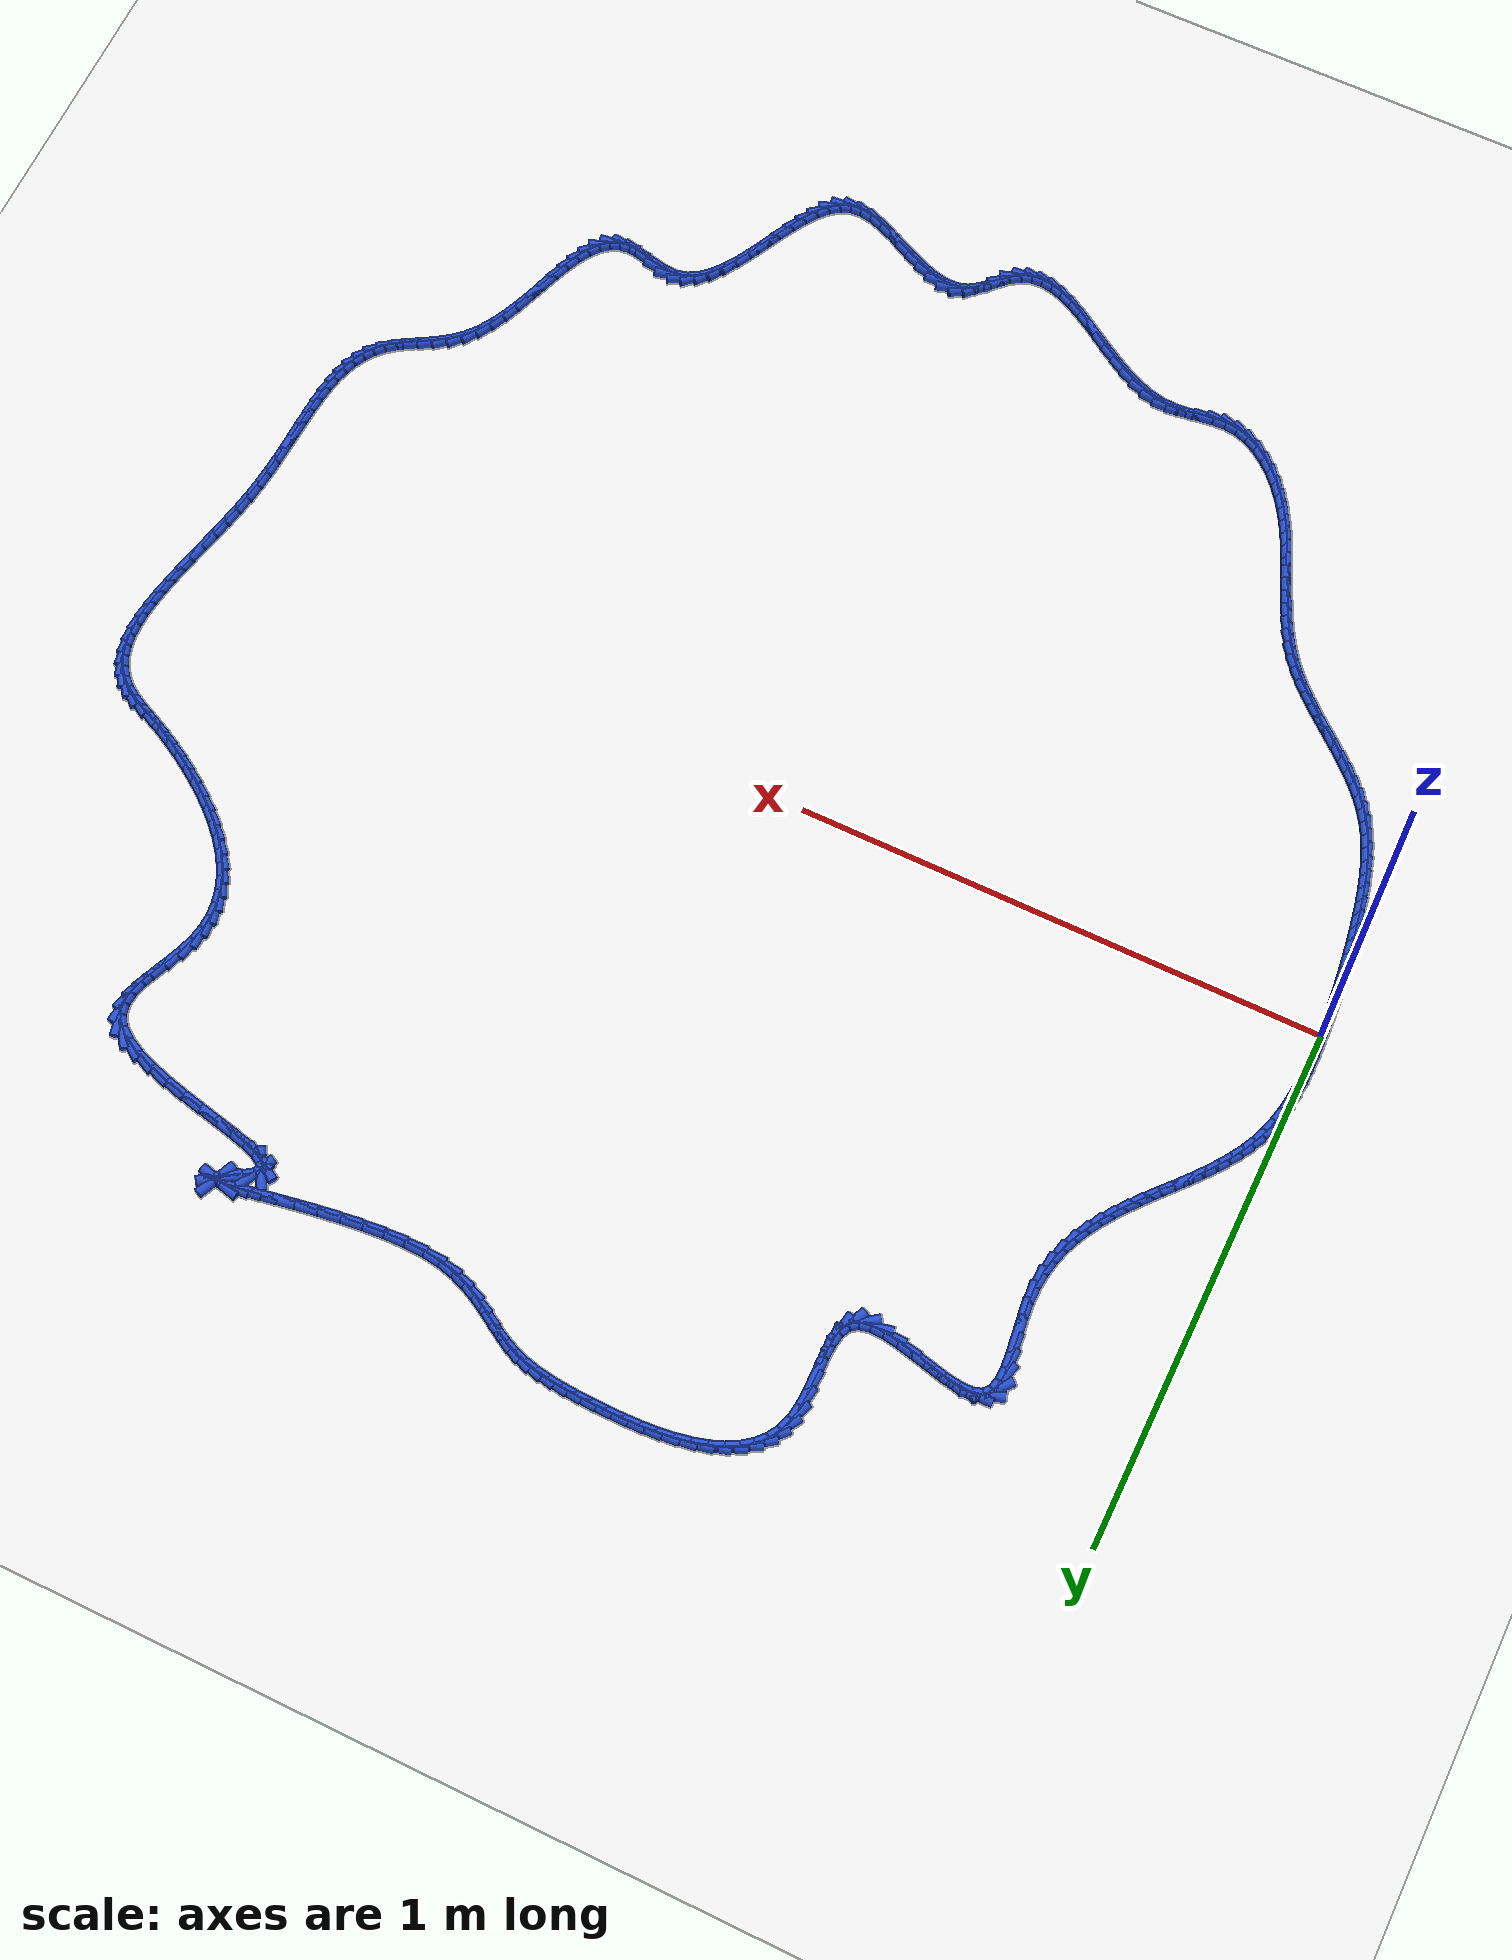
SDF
<sdf version="1.6">
 <world name="default">
  <light name="sun" type="directional">
   <pose>0 0 10 0 -0 0</pose>
   <diffuse>0.8 0.8 0.8 1</diffuse>
   <specular>0.2 0.2 0.2 1</specular>
   <attenuation>
    <range>1000</range>
    <constant>0.9</constant>
    <linear>0.01</linear>
    <quadratic>0.001</quadratic>
   </attenuation>
   <direction>-0.5 0.1 -0.9</direction>
  </light>
  <model name="ground_plane">
   <static>1</static>
   <link name="link">
    <collision name="collision">
     <geometry><plane><normal>0 0 1</normal><size>100 100</size></plane></geometry>
     <surface><friction><ode><mu>100</mu><mu2>50</mu2></ode></friction></surface>
    </collision>
    <visual name="visual">
     <cast_shadows>0</cast_shadows>
     <geometry><plane><normal>0 0 1</normal><size>100 100</size></plane></geometry>
     <material>
      <script><uri>file://media/materials/scripts/gazebo.material</uri><name>Gazebo/WhiteGlow</name></script>
     </material>
    </visual>
   </link>
  </model>
  <gravity>0 0 -9.8</gravity>
  <magnetic_field>6e-06 2.3e-05 -4.2e-05</magnetic_field>
  <atmosphere type="adiabatic"/>
  <physics name="default_physics" default="0" type="ode">
   <max_step_size>0.001</max_step_size>
   <real_time_factor>1</real_time_factor>
   <real_time_update_rate>1000</real_time_update_rate>
  </physics>
  <scene><ambient>0.4 0.4 0.4 1</ambient><background>0.7 0.7 0.7 1</background><shadows>1</shadows></scene>
  <spherical_coordinates>
   <surface_model>EARTH_WGS84</surface_model>
   <latitude_deg>0</latitude_deg>
   <longitude_deg>0</longitude_deg>
   <elevation>0</elevation>
   <heading_deg>0</heading_deg>
  </spherical_coordinates>
  <model name="line">
   <link name="link_0">
    <pose>-8.253489038045903e-18 -1.3877787807814457e-17 0.01 0 1.57 -1.5352967090500393</pose>
    <collision name="collision">
     <geometry><cylinder><radius>0.01</radius><length>0.08</length></cylinder></geometry>
    </collision>
    <visual name="visual">
     <material>
      <script><name>Gazebo/Blue</name><uri>file://media/materials/scripts/gazebo.material</uri></script>
     </material>
     <geometry><cylinder><radius>0.01</radius><length>0.08</length></cylinder></geometry>
    </visual>
   </link>
   <link name="link_1">
    <pose>-0.0009395565878767836 0.02645554884280744 0.01 0 1.57 -1.5574593401496801</pose>
    <collision name="collision">
     <geometry><cylinder><radius>0.01</radius><length>0.08</length></cylinder></geometry>
    </collision>
    <visual name="visual">
     <material>
      <script><name>Gazebo/Blue</name><uri>file://media/materials/scripts/gazebo.material</uri></script>
     </material>
     <geometry><cylinder><radius>0.01</radius><length>0.08</length></cylinder></geometry>
    </visual>
   </link>
   <link name="link_2">
    <pose>-0.0012942468446371929 0.053048454402669976 0.01 0 1.57 1.554394458003969</pose>
    <collision name="collision">
     <geometry><cylinder><radius>0.01</radius><length>0.08</length></cylinder></geometry>
    </collision>
    <visual name="visual">
     <material>
      <script><name>Gazebo/Blue</name><uri>file://media/materials/scripts/gazebo.material</uri></script>
     </material>
     <geometry><cylinder><radius>0.01</radius><length>0.08</length></cylinder></geometry>
    </visual>
   </link>
   <link name="link_3">
    <pose>-0.0008582868187953234 0.07962597044792816 0.01 0 1.57 1.5166113316829752</pose>
    <collision name="collision">
     <geometry><cylinder><radius>0.01</radius><length>0.08</length></cylinder></geometry>
    </collision>
    <visual name="visual">
     <material>
      <script><name>Gazebo/Blue</name><uri>file://media/materials/scripts/gazebo.material</uri></script>
     </material>
     <geometry><cylinder><radius>0.01</radius><length>0.08</length></cylinder></geometry>
    </visual>
   </link>
   <link name="link_4">
    <pose>0.0005741074411347346 0.10603535074692257 0.01 0 1.57 1.4701500390305338</pose>
    <collision name="collision">
     <geometry><cylinder><radius>0.01</radius><length>0.08</length></cylinder></geometry>
    </collision>
    <visual name="visual">
     <material>
      <script><name>Gazebo/Blue</name><uri>file://media/materials/scripts/gazebo.material</uri></script>
     </material>
     <geometry><cylinder><radius>0.01</radius><length>0.08</length></cylinder></geometry>
    </visual>
   </link>
   <link name="link_5">
    <pose>0.0032087198866388926 0.13212384906799385 0.01 0 1.57 1.4142644829705298</pose>
    <collision name="collision">
     <geometry><cylinder><radius>0.01</radius><length>0.08</length></cylinder></geometry>
    </collision>
    <visual name="visual">
     <material>
      <script><name>Gazebo/Blue</name><uri>file://media/materials/scripts/gazebo.material</uri></script>
     </material>
     <geometry><cylinder><radius>0.01</radius><length>0.08</length></cylinder></geometry>
    </visual>
   </link>
   <link name="link_6">
    <pose>0.007251334469203062 0.15773871917948254 0.01 0 1.57 1.3481876121108494</pose>
    <collision name="collision">
     <geometry><cylinder><radius>0.01</radius><length>0.08</length></cylinder></geometry>
    </collision>
    <visual name="visual">
     <material>
      <script><name>Gazebo/Blue</name><uri>file://media/materials/scripts/gazebo.material</uri></script>
     </material>
     <geometry><cylinder><radius>0.01</radius><length>0.08</length></cylinder></geometry>
    </visual>
   </link>
   <link name="link_7">
    <pose>0.012907735140313155 0.18272721484972923 0.01 0 1.57 1.2712814550850546</pose>
    <collision name="collision">
     <geometry><cylinder><radius>0.01</radius><length>0.08</length></cylinder></geometry>
    </collision>
    <visual name="visual">
     <material>
      <script><name>Gazebo/Blue</name><uri>file://media/materials/scripts/gazebo.material</uri></script>
     </material>
     <geometry><cylinder><radius>0.01</radius><length>0.08</length></cylinder></geometry>
    </visual>
   </link>
   <link name="link_8">
    <pose>0.020383705851455082 0.20693658984707458 0.01 0 1.57 1.1843087087483664</pose>
    <collision name="collision">
     <geometry><cylinder><radius>0.01</radius><length>0.08</length></cylinder></geometry>
    </collision>
    <visual name="visual">
     <material>
      <script><name>Gazebo/Blue</name><uri>file://media/materials/scripts/gazebo.material</uri></script>
     </material>
     <geometry><cylinder><radius>0.01</radius><length>0.08</length></cylinder></geometry>
    </visual>
   </link>
   <link name="link_9">
    <pose>0.02986229865533491 0.23022809304915437 0.01 0 1.57 1.1003042329888846</pose>
    <collision name="collision">
     <geometry><cylinder><radius>0.01</radius><length>0.08</length></cylinder></geometry>
    </collision>
    <visual name="visual">
     <material>
      <script><name>Gazebo/Blue</name><uri>file://media/materials/scripts/gazebo.material</uri></script>
     </material>
     <geometry><cylinder><radius>0.01</radius><length>0.08</length></cylinder></geometry>
    </visual>
   </link>
   <link name="link_10">
    <pose>0.04125550205563197 0.25262985618097883 0.01 0 1.57 1.028621788836884</pose>
    <collision name="collision">
     <geometry><cylinder><radius>0.01</radius><length>0.08</length></cylinder></geometry>
    </collision>
    <visual name="visual">
     <material>
      <script><name>Gazebo/Blue</name><uri>file://media/materials/scripts/gazebo.material</uri></script>
     </material>
     <geometry><cylinder><radius>0.01</radius><length>0.08</length></cylinder></geometry>
    </visual>
   </link>
   <link name="link_11">
    <pose>0.05429713827067271 0.2742797007326057 0.01 0 1.57 0.9698861675975531</pose>
    <collision name="collision">
     <geometry><cylinder><radius>0.01</radius><length>0.08</length></cylinder></geometry>
    </collision>
    <visual name="visual">
     <material>
      <script><name>Gazebo/Blue</name><uri>file://media/materials/scripts/gazebo.material</uri></script>
     </material>
     <geometry><cylinder><radius>0.01</radius><length>0.08</length></cylinder></geometry>
    </visual>
   </link>
   <link name="link_12">
    <pose>0.0687179088689758 0.29531736945177367 0.01 0 1.57 0.9239835486995319</pose>
    <collision name="collision">
     <geometry><cylinder><radius>0.01</radius><length>0.08</length></cylinder></geometry>
    </collision>
    <visual name="visual">
     <material>
      <script><name>Gazebo/Blue</name><uri>file://media/materials/scripts/gazebo.material</uri></script>
     </material>
     <geometry><cylinder><radius>0.01</radius><length>0.08</length></cylinder></geometry>
    </visual>
   </link>
   <link name="link_13">
    <pose>0.08424851541906003 0.3158826050862217 0.01 0 1.57 0.8905015614335788</pose>
    <collision name="collision">
     <geometry><cylinder><radius>0.01</radius><length>0.08</length></cylinder></geometry>
    </collision>
    <visual name="visual">
     <material>
      <script><name>Gazebo/Blue</name><uri>file://media/materials/scripts/gazebo.material</uri></script>
     </material>
     <geometry><cylinder><radius>0.01</radius><length>0.08</length></cylinder></geometry>
    </visual>
   </link>
   <link name="link_14">
    <pose>0.10061965948944408 0.33611515038368833 0.01 0 1.57 0.8689524665879704</pose>
    <collision name="collision">
     <geometry><cylinder><radius>0.01</radius><length>0.08</length></cylinder></geometry>
    </collision>
    <visual name="visual">
     <material>
      <script><name>Gazebo/Blue</name><uri>file://media/materials/scripts/gazebo.material</uri></script>
     </material>
     <geometry><cylinder><radius>0.01</radius><length>0.08</length></cylinder></geometry>
    </visual>
   </link>
   <link name="link_15">
    <pose>0.11756204264864668 0.3561547480919124 0.01 0 1.57 0.8589161430688081</pose>
    <collision name="collision">
     <geometry><cylinder><radius>0.01</radius><length>0.08</length></cylinder></geometry>
    </collision>
    <visual name="visual">
     <material>
      <script><name>Gazebo/Blue</name><uri>file://media/materials/scripts/gazebo.material</uri></script>
     </material>
     <geometry><cylinder><radius>0.01</radius><length>0.08</length></cylinder></geometry>
    </visual>
   </link>
   <link name="link_16">
    <pose>0.13480636646518654 0.3761411409586327 0.01 0 1.57 0.8601175002567543</pose>
    <collision name="collision">
     <geometry><cylinder><radius>0.01</radius><length>0.08</length></cylinder></geometry>
    </collision>
    <visual name="visual">
     <material>
      <script><name>Gazebo/Blue</name><uri>file://media/materials/scripts/gazebo.material</uri></script>
     </material>
     <geometry><cylinder><radius>0.01</radius><length>0.08</length></cylinder></geometry>
    </visual>
   </link>
   <link name="link_17">
    <pose>0.15208333250758235 0.39621407173158774 0.01 0 1.57 0.8724551031376572</pose>
    <collision name="collision">
     <geometry><cylinder><radius>0.01</radius><length>0.08</length></cylinder></geometry>
    </collision>
    <visual name="visual">
     <material>
      <script><name>Gazebo/Blue</name><uri>file://media/materials/scripts/gazebo.material</uri></script>
     </material>
     <geometry><cylinder><radius>0.01</radius><length>0.08</length></cylinder></geometry>
    </visual>
   </link>
   <link name="link_18">
    <pose>0.1691236423443529 0.41651328315851643 0.01 0 1.57 0.8959914375994646</pose>
    <collision name="collision">
     <geometry><cylinder><radius>0.01</radius><length>0.08</length></cylinder></geometry>
    </collision>
    <visual name="visual">
     <material>
      <script><name>Gazebo/Blue</name><uri>file://media/materials/scripts/gazebo.material</uri></script>
     </material>
     <geometry><cylinder><radius>0.01</radius><length>0.08</length></cylinder></geometry>
    </visual>
   </link>
   <link name="link_19">
    <pose>0.18565799754401682 0.43717851798715757 0.01 0 1.57 0.9309068245905547</pose>
    <collision name="collision">
     <geometry><cylinder><radius>0.01</radius><length>0.08</length></cylinder></geometry>
    </collision>
    <visual name="visual">
     <material>
      <script><name>Gazebo/Blue</name><uri>file://media/materials/scripts/gazebo.material</uri></script>
     </material>
     <geometry><cylinder><radius>0.01</radius><length>0.08</length></cylinder></geometry>
    </visual>
   </link>
   <link name="link_20">
    <pose>0.20141709967509303 0.4583495189652499 0.01 0 1.57 0.9774118242091248</pose>
    <collision name="collision">
     <geometry><cylinder><radius>0.01</radius><length>0.08</length></cylinder></geometry>
    </collision>
    <visual name="visual">
     <material>
      <script><name>Gazebo/Blue</name><uri>file://media/materials/scripts/gazebo.material</uri></script>
     </material>
     <geometry><cylinder><radius>0.01</radius><length>0.08</length></cylinder></geometry>
    </visual>
   </link>
   <link name="link_21">
    <pose>0.2161316503061 0.480166028840532 0.01 0 1.57 1.0356099639411565</pose>
    <collision name="collision">
     <geometry><cylinder><radius>0.01</radius><length>0.08</length></cylinder></geometry>
    </collision>
    <visual name="visual">
     <material>
      <script><name>Gazebo/Blue</name><uri>file://media/materials/scripts/gazebo.material</uri></script>
     </material>
     <geometry><cylinder><radius>0.01</radius><length>0.08</length></cylinder></geometry>
    </visual>
   </link>
   <link name="link_22">
    <pose>0.22953235100555655 0.5027677903607427 0.01 0 1.57 1.1053082781964698</pose>
    <collision name="collision">
     <geometry><cylinder><radius>0.01</radius><length>0.08</length></cylinder></geometry>
    </collision>
    <visual name="visual">
     <material>
      <script><name>Gazebo/Blue</name><uri>file://media/materials/scripts/gazebo.material</uri></script>
     </material>
     <geometry><cylinder><radius>0.01</radius><length>0.08</length></cylinder></geometry>
    </visual>
   </link>
   <link name="link_23">
    <pose>0.2413499033419814 0.5262945462736206 0.01 0 1.57 1.1857931498995955</pose>
    <collision name="collision">
     <geometry><cylinder><radius>0.01</radius><length>0.08</length></cylinder></geometry>
    </collision>
    <visual name="visual">
     <material>
      <script><name>Gazebo/Blue</name><uri>file://media/materials/scripts/gazebo.material</uri></script>
     </material>
     <geometry><cylinder><radius>0.01</radius><length>0.08</length></cylinder></geometry>
    </visual>
   </link>
   <link name="link_24">
    <pose>0.2513150088838933 0.5508860393269048 0.01 0 1.57 1.2756247281346937</pose>
    <collision name="collision">
     <geometry><cylinder><radius>0.01</radius><length>0.08</length></cylinder></geometry>
    </collision>
    <visual name="visual">
     <material>
      <script><name>Gazebo/Blue</name><uri>file://media/materials/scripts/gazebo.material</uri></script>
     </material>
     <geometry><cylinder><radius>0.01</radius><length>0.08</length></cylinder></geometry>
    </visual>
   </link>
   <link name="link_25">
    <pose>0.259158369199811 0.5766820122683338 0.01 0 1.57 1.372540796333877</pose>
    <collision name="collision">
     <geometry><cylinder><radius>0.01</radius><length>0.08</length></cylinder></geometry>
    </collision>
    <visual name="visual">
     <material>
      <script><name>Gazebo/Blue</name><uri>file://media/materials/scripts/gazebo.material</uri></script>
     </material>
     <geometry><cylinder><radius>0.01</radius><length>0.08</length></cylinder></geometry>
    </visual>
   </link>
   <link name="link_26">
    <pose>0.26461068585825315 0.6038222078456463 0.01 0 1.57 1.4735648093288154</pose>
    <collision name="collision">
     <geometry><cylinder><radius>0.01</radius><length>0.08</length></cylinder></geometry>
    </collision>
    <visual name="visual">
     <material>
      <script><name>Gazebo/Blue</name><uri>file://media/materials/scripts/gazebo.material</uri></script>
     </material>
     <geometry><cylinder><radius>0.01</radius><length>0.08</length></cylinder></geometry>
    </visual>
   </link>
   <link name="link_27">
    <pose>0.2674026604277384 0.6324463688065811 0.01 0 1.57 -1.5663842565983226</pose>
    <collision name="collision">
     <geometry><cylinder><radius>0.01</radius><length>0.08</length></cylinder></geometry>
    </collision>
    <visual name="visual">
     <material>
      <script><name>Gazebo/Blue</name><uri>file://media/materials/scripts/gazebo.material</uri></script>
     </material>
     <geometry><cylinder><radius>0.01</radius><length>0.08</length></cylinder></geometry>
    </visual>
   </link>
   <link name="link_28">
    <pose>0.2672692192843914 0.6626907374429276 0.01 0 1.57 -1.4828766486269551</pose>
    <collision name="collision">
     <geometry><cylinder><radius>0.01</radius><length>0.08</length></cylinder></geometry>
    </collision>
    <visual name="visual">
     <material>
      <script><name>Gazebo/Blue</name><uri>file://media/materials/scripts/gazebo.material</uri></script>
     </material>
     <geometry><cylinder><radius>0.01</radius><length>0.08</length></cylinder></geometry>
    </visual>
   </link>
   <link name="link_29">
    <pose>0.26448808860806705 0.69424182034737 0.01 0 1.57 -1.442635872046809</pose>
    <collision name="collision">
     <geometry><cylinder><radius>0.01</radius><length>0.08</length></cylinder></geometry>
    </collision>
    <visual name="visual">
     <material>
      <script><name>Gazebo/Blue</name><uri>file://media/materials/scripts/gazebo.material</uri></script>
     </material>
     <geometry><cylinder><radius>0.01</radius><length>0.08</length></cylinder></geometry>
    </visual>
   </link>
   <link name="link_30">
    <pose>0.2604086300167814 0.725898222699114 0.01 0 1.57 -1.443345490882644</pose>
    <collision name="collision">
     <geometry><cylinder><radius>0.01</radius><length>0.08</length></cylinder></geometry>
    </collision>
    <visual name="visual">
     <material>
      <script><name>Gazebo/Blue</name><uri>file://media/materials/scripts/gazebo.material</uri></script>
     </material>
     <geometry><cylinder><radius>0.01</radius><length>0.08</length></cylinder></geometry>
    </visual>
   </link>
   <link name="link_31">
    <pose>0.2565057982388003 0.7563544897553595 0.01 0 1.57 -1.4904261472061475</pose>
    <collision name="collision">
     <geometry><cylinder><radius>0.01</radius><length>0.08</length></cylinder></geometry>
    </collision>
    <visual name="visual">
     <material>
      <script><name>Gazebo/Blue</name><uri>file://media/materials/scripts/gazebo.material</uri></script>
     </material>
     <geometry><cylinder><radius>0.01</radius><length>0.08</length></cylinder></geometry>
    </visual>
   </link>
   <link name="link_32">
    <pose>0.2542545480023896 0.7843051667733064 0.01 0 1.57 1.534552910283694</pose>
    <collision name="collision">
     <geometry><cylinder><radius>0.01</radius><length>0.08</length></cylinder></geometry>
    </collision>
    <visual name="visual">
     <material>
      <script><name>Gazebo/Blue</name><uri>file://media/materials/scripts/gazebo.material</uri></script>
     </material>
     <geometry><cylinder><radius>0.01</radius><length>0.08</length></cylinder></geometry>
    </visual>
   </link>
   <link name="link_33">
    <pose>0.2551298340358152 0.8084447990101546 0.01 0 1.57 1.2904762506047198</pose>
    <collision name="collision">
     <geometry><cylinder><radius>0.01</radius><length>0.08</length></cylinder></geometry>
    </collision>
    <visual name="visual">
     <material>
      <script><name>Gazebo/Blue</name><uri>file://media/materials/scripts/gazebo.material</uri></script>
     </material>
     <geometry><cylinder><radius>0.01</radius><length>0.08</length></cylinder></geometry>
    </visual>
   </link>
   <link name="link_34">
    <pose>0.2606066110673428 0.827467931723104 0.01 0 1.57 0.8289813421498567</pose>
    <collision name="collision">
     <geometry><cylinder><radius>0.01</radius><length>0.08</length></cylinder></geometry>
    </collision>
    <visual name="visual">
     <material>
      <script><name>Gazebo/Blue</name><uri>file://media/materials/scripts/gazebo.material</uri></script>
     </material>
     <geometry><cylinder><radius>0.01</radius><length>0.08</length></cylinder></geometry>
    </visual>
   </link>
   <link name="link_35">
    <pose>0.2721570786431589 0.840071788592008 0.01 0 1.57 0.2996460380054777</pose>
    <collision name="collision">
     <geometry><cylinder><radius>0.01</radius><length>0.08</length></cylinder></geometry>
    </collision>
    <visual name="visual">
     <material>
      <script><name>Gazebo/Blue</name><uri>file://media/materials/scripts/gazebo.material</uri></script>
     </material>
     <geometry><cylinder><radius>0.01</radius><length>0.08</length></cylinder></geometry>
    </visual>
   </link>
   <link name="link_36">
    <pose>0.29045881077669766 0.8457260805467023 0.01 0 1.57 0.0004749256121031723</pose>
    <collision name="collision">
     <geometry><cylinder><radius>0.01</radius><length>0.08</length></cylinder></geometry>
    </collision>
    <visual name="visual">
     <material>
      <script><name>Gazebo/Blue</name><uri>file://media/materials/scripts/gazebo.material</uri></script>
     </material>
     <geometry><cylinder><radius>0.01</radius><length>0.08</length></cylinder></geometry>
    </visual>
   </link>
   <link name="link_37">
    <pose>0.31429985446935593 0.8457374032698225 0.01 0 1.57 -0.1444653741208271</pose>
    <collision name="collision">
     <geometry><cylinder><radius>0.01</radius><length>0.08</length></cylinder></geometry>
    </collision>
    <visual name="visual">
     <material>
      <script><name>Gazebo/Blue</name><uri>file://media/materials/scripts/gazebo.material</uri></script>
     </material>
     <geometry><cylinder><radius>0.01</radius><length>0.08</length></cylinder></geometry>
    </visual>
   </link>
   <link name="link_38">
    <pose>0.34219348366471025 0.8416794703190987 0.01 0 1.57 -0.2119231707341669</pose>
    <collision name="collision">
     <geometry><cylinder><radius>0.01</radius><length>0.08</length></cylinder></geometry>
    </collision>
    <visual name="visual">
     <material>
      <script><name>Gazebo/Blue</name><uri>file://media/materials/scripts/gazebo.material</uri></script>
     </material>
     <geometry><cylinder><radius>0.01</radius><length>0.08</length></cylinder></geometry>
    </visual>
   </link>
   <link name="link_39">
    <pose>0.3726529723063379 0.835125995252261 0.01 0 1.57 -0.23272596432569825</pose>
    <collision name="collision">
     <geometry><cylinder><radius>0.01</radius><length>0.08</length></cylinder></geometry>
    </collision>
    <visual name="visual">
     <material>
      <script><name>Gazebo/Blue</name><uri>file://media/materials/scripts/gazebo.material</uri></script>
     </material>
     <geometry><cylinder><radius>0.01</radius><length>0.08</length></cylinder></geometry>
    </visual>
   </link>
   <link name="link_40">
    <pose>0.40419159433781526 0.8276506916270395 0.01 0 1.57 -0.21577169232652965</pose>
    <collision name="collision">
     <geometry><cylinder><radius>0.01</radius><length>0.08</length></cylinder></geometry>
    </collision>
    <visual name="visual">
     <material>
      <script><name>Gazebo/Blue</name><uri>file://media/materials/scripts/gazebo.material</uri></script>
     </material>
     <geometry><cylinder><radius>0.01</radius><length>0.08</length></cylinder></geometry>
    </visual>
   </link>
   <link name="link_41">
    <pose>0.4353226237027193 0.8208272730011645 0.01 0 1.57 -0.1559843534359159</pose>
    <collision name="collision">
     <geometry><cylinder><radius>0.01</radius><length>0.08</length></cylinder></geometry>
    </collision>
    <visual name="visual">
     <material>
      <script><name>Gazebo/Blue</name><uri>file://media/materials/scripts/gazebo.material</uri></script>
     </material>
     <geometry><cylinder><radius>0.01</radius><length>0.08</length></cylinder></geometry>
    </visual>
   </link>
   <link name="link_42">
    <pose>0.46455933434462693 0.816229452932366 0.01 0 1.57 -0.030873474198297505</pose>
    <collision name="collision">
     <geometry><cylinder><radius>0.01</radius><length>0.08</length></cylinder></geometry>
    </collision>
    <visual name="visual">
     <material>
      <script><name>Gazebo/Blue</name><uri>file://media/materials/scripts/gazebo.material</uri></script>
     </material>
     <geometry><cylinder><radius>0.01</radius><length>0.08</length></cylinder></geometry>
    </visual>
   </link>
   <link name="link_43">
    <pose>0.49041500020711426 0.8154309449783738 0.01 0 1.57 0.21460347535287516</pose>
    <collision name="collision">
     <geometry><cylinder><radius>0.01</radius><length>0.08</length></cylinder></geometry>
    </collision>
    <visual name="visual">
     <material>
      <script><name>Gazebo/Blue</name><uri>file://media/materials/scripts/gazebo.material</uri></script>
     </material>
     <geometry><cylinder><radius>0.01</radius><length>0.08</length></cylinder></geometry>
    </visual>
   </link>
   <link name="link_44">
    <pose>0.511402895233759 0.8200054626969184 0.01 0 1.57 0.6607189357446506</pose>
    <collision name="collision">
     <geometry><cylinder><radius>0.01</radius><length>0.08</length></cylinder></geometry>
    </collision>
    <visual name="visual">
     <material>
      <script><name>Gazebo/Blue</name><uri>file://media/materials/scripts/gazebo.material</uri></script>
     </material>
     <geometry><cylinder><radius>0.01</radius><length>0.08</length></cylinder></geometry>
    </visual>
   </link>
   <link name="link_45">
    <pose>0.5261187217249939 0.8314434497185448 0.01 0 1.57 1.1306768266454448</pose>
    <collision name="collision">
     <geometry><cylinder><radius>0.01</radius><length>0.08</length></cylinder></geometry>
    </collision>
    <visual name="visual">
     <material>
      <script><name>Gazebo/Blue</name><uri>file://media/materials/scripts/gazebo.material</uri></script>
     </material>
     <geometry><cylinder><radius>0.01</radius><length>0.08</length></cylinder></geometry>
    </visual>
   </link>
   <link name="link_46">
    <pose>0.5347039005766825 0.8496738497264652 0.01 0 1.57 1.4039304632642877</pose>
    <collision name="collision">
     <geometry><cylinder><radius>0.01</radius><length>0.08</length></cylinder></geometry>
    </collision>
    <visual name="visual">
     <material>
      <script><name>Gazebo/Blue</name><uri>file://media/materials/scripts/gazebo.material</uri></script>
     </material>
     <geometry><cylinder><radius>0.01</radius><length>0.08</length></cylinder></geometry>
    </visual>
   </link>
   <link name="link_47">
    <pose>0.5386729427292178 0.8732384974963888 0.01 0 1.57 1.5373993321435813</pose>
    <collision name="collision">
     <geometry><cylinder><radius>0.01</radius><length>0.08</length></cylinder></geometry>
    </collision>
    <visual name="visual">
     <material>
      <script><name>Gazebo/Blue</name><uri>file://media/materials/scripts/gazebo.material</uri></script>
     </material>
     <geometry><cylinder><radius>0.01</radius><length>0.08</length></cylinder></geometry>
    </visual>
   </link>
   <link name="link_48">
    <pose>0.5395881099100085 0.9006309894949102 0.01 0 1.57 -1.5513989023679933</pose>
    <collision name="collision">
     <geometry><cylinder><radius>0.01</radius><length>0.08</length></cylinder></geometry>
    </collision>
    <visual name="visual">
     <material>
      <script><name>Gazebo/Blue</name><uri>file://media/materials/scripts/gazebo.material</uri></script>
     </material>
     <geometry><cylinder><radius>0.01</radius><length>0.08</length></cylinder></geometry>
    </visual>
   </link>
   <link name="link_49">
    <pose>0.5390116638464629 0.9303449221886234 0.01 0 1.57 -1.5542300518301515</pose>
    <collision name="collision">
     <geometry><cylinder><radius>0.01</radius><length>0.08</length></cylinder></geometry>
    </collision>
    <visual name="visual">
     <material>
      <script><name>Gazebo/Blue</name><uri>file://media/materials/scripts/gazebo.material</uri></script>
     </material>
     <geometry><cylinder><radius>0.01</radius><length>0.08</length></cylinder></geometry>
    </visual>
   </link>
   <link name="link_50">
    <pose>0.5385058662659898 0.9608738920441238 0.01 0 1.57 1.5330393742134707</pose>
    <collision name="collision">
     <geometry><cylinder><radius>0.01</radius><length>0.08</length></cylinder></geometry>
    </collision>
    <visual name="visual">
     <material>
      <script><name>Gazebo/Blue</name><uri>file://media/materials/scripts/gazebo.material</uri></script>
     </material>
     <geometry><cylinder><radius>0.01</radius><length>0.08</length></cylinder></geometry>
    </visual>
   </link>
   <link name="link_51">
    <pose>0.5396329788959975 0.9907114955280049 0.01 0 1.57 1.4156758449845734</pose>
    <collision name="collision">
     <geometry><cylinder><radius>0.01</radius><length>0.08</length></cylinder></geometry>
    </collision>
    <visual name="visual">
     <material>
      <script><name>Gazebo/Blue</name><uri>file://media/materials/scripts/gazebo.material</uri></script>
     </material>
     <geometry><cylinder><radius>0.01</radius><length>0.08</length></cylinder></geometry>
    </visual>
   </link>
   <link name="link_52">
    <pose>0.5439552134179969 1.0183513726422542 0.01 0 1.57 1.2270328774771515</pose>
    <collision name="collision">
     <geometry><cylinder><radius>0.01</radius><length>0.08</length></cylinder></geometry>
    </collision>
    <visual name="visual">
     <material>
      <script><name>Gazebo/Blue</name><uri>file://media/materials/scripts/gazebo.material</uri></script>
     </material>
     <geometry><cylinder><radius>0.01</radius><length>0.08</length></cylinder></geometry>
    </visual>
   </link>
   <link name="link_53">
    <pose>0.5526450417346751 1.042626201647599 0.01 0 1.57 1.017795693699068</pose>
    <collision name="collision">
     <geometry><cylinder><radius>0.01</radius><length>0.08</length></cylinder></geometry>
    </collision>
    <visual name="visual">
     <material>
      <script><name>Gazebo/Blue</name><uri>file://media/materials/scripts/gazebo.material</uri></script>
     </material>
     <geometry><cylinder><radius>0.01</radius><length>0.08</length></cylinder></geometry>
    </visual>
   </link>
   <link name="link_54">
    <pose>0.5655450038613138 1.0635255809239053 0.01 0 1.57 0.8170722181826445</pose>
    <collision name="collision">
     <geometry><cylinder><radius>0.01</radius><length>0.08</length></cylinder></geometry>
    </collision>
    <visual name="visual">
     <material>
      <script><name>Gazebo/Blue</name><uri>file://media/materials/scripts/gazebo.material</uri></script>
     </material>
     <geometry><cylinder><radius>0.01</radius><length>0.08</length></cylinder></geometry>
    </visual>
   </link>
   <link name="link_55">
    <pose>0.5822142099452967 1.0812856671294306 0.01 0 1.57 0.6389661651674776</pose>
    <collision name="collision">
     <geometry><cylinder><radius>0.01</radius><length>0.08</length></cylinder></geometry>
    </collision>
    <visual name="visual">
     <material>
      <script><name>Gazebo/Blue</name><uri>file://media/materials/scripts/gazebo.material</uri></script>
     </material>
     <geometry><cylinder><radius>0.01</radius><length>0.08</length></cylinder></geometry>
    </visual>
   </link>
   <link name="link_56">
    <pose>0.6022117701340077 1.096142616922432 0.01 0 1.57 0.48943407880741896</pose>
    <collision name="collision">
     <geometry><cylinder><radius>0.01</radius><length>0.08</length></cylinder></geometry>
    </collision>
    <visual name="visual">
     <material>
      <script><name>Gazebo/Blue</name><uri>file://media/materials/scripts/gazebo.material</uri></script>
     </material>
     <geometry><cylinder><radius>0.01</radius><length>0.08</length></cylinder></geometry>
    </visual>
   </link>
   <link name="link_57">
    <pose>0.6250967945748307 1.108332586961167 0.01 0 1.57 0.3677316555457081</pose>
    <collision name="collision">
     <geometry><cylinder><radius>0.01</radius><length>0.08</length></cylinder></geometry>
    </collision>
    <visual name="visual">
     <material>
      <script><name>Gazebo/Blue</name><uri>file://media/materials/scripts/gazebo.material</uri></script>
     </material>
     <geometry><cylinder><radius>0.01</radius><length>0.08</length></cylinder></geometry>
    </visual>
   </link>
   <link name="link_58">
    <pose>0.6504283934151496 1.1180917339038925 0.01 0 1.57 0.2699546364870247</pose>
    <collision name="collision">
     <geometry><cylinder><radius>0.01</radius><length>0.08</length></cylinder></geometry>
    </collision>
    <visual name="visual">
     <material>
      <script><name>Gazebo/Blue</name><uri>file://media/materials/scripts/gazebo.material</uri></script>
     </material>
     <geometry><cylinder><radius>0.01</radius><length>0.08</length></cylinder></geometry>
    </visual>
   </link>
   <link name="link_59">
    <pose>0.677765676802348 1.125656214408866 0.01 0 1.57 0.19158530284460423</pose>
    <collision name="collision">
     <geometry><cylinder><radius>0.01</radius><length>0.08</length></cylinder></geometry>
    </collision>
    <visual name="visual">
     <material>
      <script><name>Gazebo/Blue</name><uri>file://media/materials/scripts/gazebo.material</uri></script>
     </material>
     <geometry><cylinder><radius>0.01</radius><length>0.08</length></cylinder></geometry>
    </visual>
   </link>
   <link name="link_60">
    <pose>0.7066677548838103 1.131262185134345 0.01 0 1.57 0.1286277842384979</pose>
    <collision name="collision">
     <geometry><cylinder><radius>0.01</radius><length>0.08</length></cylinder></geometry>
    </collision>
    <visual name="visual">
     <material>
      <script><name>Gazebo/Blue</name><uri>file://media/materials/scripts/gazebo.material</uri></script>
     </material>
     <geometry><cylinder><radius>0.01</radius><length>0.08</length></cylinder></geometry>
    </visual>
   </link>
   <link name="link_61">
    <pose>0.7366937378069199 1.1351458027385861 0.01 0 1.57 0.07791098571765774</pose>
    <collision name="collision">
     <geometry><cylinder><radius>0.01</radius><length>0.08</length></cylinder></geometry>
    </collision>
    <visual name="visual">
     <material>
      <script><name>Gazebo/Blue</name><uri>file://media/materials/scripts/gazebo.material</uri></script>
     </material>
     <geometry><cylinder><radius>0.01</radius><length>0.08</length></cylinder></geometry>
    </visual>
   </link>
   <link name="link_62">
    <pose>0.7674027357190609 1.1375432238798475 0.01 0 1.57 0.03705378234773313</pose>
    <collision name="collision">
     <geometry><cylinder><radius>0.01</radius><length>0.08</length></cylinder></geometry>
    </collision>
    <visual name="visual">
     <material>
      <script><name>Gazebo/Blue</name><uri>file://media/materials/scripts/gazebo.material</uri></script>
     </material>
     <geometry><cylinder><radius>0.01</radius><length>0.08</length></cylinder></geometry>
    </visual>
   </link>
   <link name="link_63">
    <pose>0.7983538587676173 1.1386906052163857 0.01 0 1.57 0.0043410443534745765</pose>
    <collision name="collision">
     <geometry><cylinder><radius>0.01</radius><length>0.08</length></cylinder></geometry>
    </collision>
    <visual name="visual">
     <material>
      <script><name>Gazebo/Blue</name><uri>file://media/materials/scripts/gazebo.material</uri></script>
     </material>
     <geometry><cylinder><radius>0.01</radius><length>0.08</length></cylinder></geometry>
    </visual>
   </link>
   <link name="link_64">
    <pose>0.8291062170999728 1.1388241034064577 0.01 0 1.57 -0.021390641059624214</pose>
    <collision name="collision">
     <geometry><cylinder><radius>0.01</radius><length>0.08</length></cylinder></geometry>
    </collision>
    <visual name="visual">
     <material>
      <script><name>Gazebo/Blue</name><uri>file://media/materials/scripts/gazebo.material</uri></script>
     </material>
     <geometry><cylinder><radius>0.01</radius><length>0.08</length></cylinder></geometry>
    </visual>
   </link>
   <link name="link_65">
    <pose>0.8592189208635113 1.1381798751083216 0.01 0 1.57 -0.04193806316624282</pose>
    <collision name="collision">
     <geometry><cylinder><radius>0.01</radius><length>0.08</length></cylinder></geometry>
    </collision>
    <visual name="visual">
     <material>
      <script><name>Gazebo/Blue</name><uri>file://media/materials/scripts/gazebo.material</uri></script>
     </material>
     <geometry><cylinder><radius>0.01</radius><length>0.08</length></cylinder></geometry>
    </visual>
   </link>
   <link name="link_66">
    <pose>0.8882778101295206 1.1369604866036076 0.01 0 1.57 -0.06831897836503452</pose>
    <collision name="collision">
     <geometry><cylinder><radius>0.01</radius><length>0.08</length></cylinder></geometry>
    </collision>
    <visual name="visual">
     <material>
      <script><name>Gazebo/Blue</name><uri>file://media/materials/scripts/gazebo.material</uri></script>
     </material>
     <geometry><cylinder><radius>0.01</radius><length>0.08</length></cylinder></geometry>
    </visual>
   </link>
   <link name="link_67">
    <pose>0.9161177829901833 1.1350555233830575 0.01 0 1.57 -0.10756076932836463</pose>
    <collision name="collision">
     <geometry><cylinder><radius>0.01</radius><length>0.08</length></cylinder></geometry>
    </collision>
    <visual name="visual">
     <material>
      <script><name>Gazebo/Blue</name><uri>file://media/materials/scripts/gazebo.material</uri></script>
     </material>
     <geometry><cylinder><radius>0.01</radius><length>0.08</length></cylinder></geometry>
    </visual>
   </link>
   <link name="link_68">
    <pose>0.9427092803237068 1.1321842399911701 0.01 0 1.57 -0.16133808008794162</pose>
    <collision name="collision">
     <geometry><cylinder><radius>0.01</radius><length>0.08</length></cylinder></geometry>
    </collision>
    <visual name="visual">
     <material>
      <script><name>Gazebo/Blue</name><uri>file://media/materials/scripts/gazebo.material</uri></script>
     </material>
     <geometry><cylinder><radius>0.01</radius><length>0.08</length></cylinder></geometry>
    </visual>
   </link>
   <link name="link_69">
    <pose>0.9680241005581061 1.1280641849964166 0.01 0 1.57 -0.23116485977365064</pose>
    <collision name="collision">
     <geometry><cylinder><radius>0.01</radius><length>0.08</length></cylinder></geometry>
    </collision>
    <visual name="visual">
     <material>
      <script><name>Gazebo/Blue</name><uri>file://media/materials/scripts/gazebo.material</uri></script>
     </material>
     <geometry><cylinder><radius>0.01</radius><length>0.08</length></cylinder></geometry>
    </visual>
   </link>
   <link name="link_70">
    <pose>0.9920340421213966 1.1224129069672686 0.01 0 1.57 -0.3180152008030883</pose>
    <collision name="collision">
     <geometry><cylinder><radius>0.01</radius><length>0.08</length></cylinder></geometry>
    </collision>
    <visual name="visual">
     <material>
      <script><name>Gazebo/Blue</name><uri>file://media/materials/scripts/gazebo.material</uri></script>
     </material>
     <geometry><cylinder><radius>0.01</radius><length>0.08</length></cylinder></geometry>
    </visual>
   </link>
   <link name="link_71">
    <pose>1.0147109034415942 1.1149479544721979 0.01 0 1.57 -0.41819017896109345</pose>
    <collision name="collision">
     <geometry><cylinder><radius>0.01</radius><length>0.08</length></cylinder></geometry>
    </collision>
    <visual name="visual">
     <material>
      <script><name>Gazebo/Blue</name><uri>file://media/materials/scripts/gazebo.material</uri></script>
     </material>
     <geometry><cylinder><radius>0.01</radius><length>0.08</length></cylinder></geometry>
    </visual>
   </link>
   <link name="link_72">
    <pose>1.0360757871048465 1.1054533243558418 0.01 0 1.57 -0.4987269559054551</pose>
    <collision name="collision">
     <geometry><cylinder><radius>0.01</radius><length>0.08</length></cylinder></geometry>
    </collision>
    <visual name="visual">
     <material>
      <script><name>Gazebo/Blue</name><uri>file://media/materials/scripts/gazebo.material</uri></script>
     </material>
     <geometry><cylinder><radius>0.01</radius><length>0.08</length></cylinder></geometry>
    </visual>
   </link>
   <link name="link_73">
    <pose>1.0565762387082873 1.0942877398964 0.01 0 1.57 -0.5404997946324268</pose>
    <collision name="collision">
     <geometry><cylinder><radius>0.01</radius><length>0.08</length></cylinder></geometry>
    </collision>
    <visual name="visual">
     <material>
      <script><name>Gazebo/Blue</name><uri>file://media/materials/scripts/gazebo.material</uri></script>
     </material>
     <geometry><cylinder><radius>0.01</radius><length>0.08</length></cylinder></geometry>
    </visual>
   </link>
   <link name="link_74">
    <pose>1.076878243362914 1.0821043200111564 0.01 0 1.57 -0.5433510634614989</pose>
    <collision name="collision">
     <geometry><cylinder><radius>0.01</radius><length>0.08</length></cylinder></geometry>
    </collision>
    <visual name="visual">
     <material>
      <script><name>Gazebo/Blue</name><uri>file://media/materials/scripts/gazebo.material</uri></script>
     </material>
     <geometry><cylinder><radius>0.01</radius><length>0.08</length></cylinder></geometry>
    </visual>
   </link>
   <link name="link_75">
    <pose>1.097649557917581 1.069558571426675 0.01 0 1.57 -0.5099279092797003</pose>
    <collision name="collision">
     <geometry><cylinder><radius>0.01</radius><length>0.08</length></cylinder></geometry>
    </collision>
    <visual name="visual">
     <material>
      <script><name>Gazebo/Blue</name><uri>file://media/materials/scripts/gazebo.material</uri></script>
     </material>
     <geometry><cylinder><radius>0.01</radius><length>0.08</length></cylinder></geometry>
    </visual>
   </link>
   <link name="link_76">
    <pose>1.119557939221141 1.0573060008695208 0.01 0 1.57 -0.4448276325542376</pose>
    <collision name="collision">
     <geometry><cylinder><radius>0.01</radius><length>0.08</length></cylinder></geometry>
    </collision>
    <visual name="visual">
     <material>
      <script><name>Gazebo/Blue</name><uri>file://media/materials/scripts/gazebo.material</uri></script>
     </material>
     <geometry><cylinder><radius>0.01</radius><length>0.08</length></cylinder></geometry>
    </visual>
   </link>
   <link name="link_77">
    <pose>1.1432711441224492 1.0460021150662575 0.01 0 1.57 -0.3547478070886102</pose>
    <collision name="collision">
     <geometry><cylinder><radius>0.01</radius><length>0.08</length></cylinder></geometry>
    </collision>
    <visual name="visual">
     <material>
      <script><name>Gazebo/Blue</name><uri>file://media/materials/scripts/gazebo.material</uri></script>
     </material>
     <geometry><cylinder><radius>0.01</radius><length>0.08</length></cylinder></geometry>
    </visual>
   </link>
   <link name="link_78">
    <pose>1.1694569294703592 1.03630242074345 0.01 0 1.57 -0.2484566530718259</pose>
    <collision name="collision">
     <geometry><cylinder><radius>0.01</radius><length>0.08</length></cylinder></geometry>
    </collision>
    <visual name="visual">
     <material>
      <script><name>Gazebo/Blue</name><uri>file://media/materials/scripts/gazebo.material</uri></script>
     </material>
     <geometry><cylinder><radius>0.01</radius><length>0.08</length></cylinder></geometry>
    </visual>
   </link>
   <link name="link_79">
    <pose>1.1987830521137246 1.0288624246276619 0.01 0 1.57 -0.13606380426584513</pose>
    <collision name="collision">
     <geometry><cylinder><radius>0.01</radius><length>0.08</length></cylinder></geometry>
    </collision>
    <visual name="visual">
     <material>
      <script><name>Gazebo/Blue</name><uri>file://media/materials/scripts/gazebo.material</uri></script>
     </material>
     <geometry><cylinder><radius>0.01</radius><length>0.08</length></cylinder></geometry>
    </visual>
   </link>
   <link name="link_80">
    <pose>1.2319029323683126 1.0243279905908655 0.01 0 1.57 -0.03921163434594837</pose>
    <collision name="collision">
     <geometry><cylinder><radius>0.01</radius><length>0.08</length></cylinder></geometry>
    </collision>
    <visual name="visual">
     <material>
      <script><name>Gazebo/Blue</name><uri>file://media/materials/scripts/gazebo.material</uri></script>
     </material>
     <geometry><cylinder><radius>0.01</radius><length>0.08</length></cylinder></geometry>
    </visual>
   </link>
   <link name="link_81">
    <pose>1.2687804902889022 1.022881219702808 0.01 0 1.57 0.029356387651383205</pose>
    <collision name="collision">
     <geometry><cylinder><radius>0.01</radius><length>0.08</length></cylinder></geometry>
    </collision>
    <visual name="visual">
     <material>
      <script><name>Gazebo/Blue</name><uri>file://media/materials/scripts/gazebo.material</uri></script>
     </material>
     <geometry><cylinder><radius>0.01</radius><length>0.08</length></cylinder></geometry>
    </visual>
   </link>
   <link name="link_82">
    <pose>1.308398979292533 1.0240446096455431 0.01 0 1.57 0.07848825222287074</pose>
    <collision name="collision">
     <geometry><cylinder><radius>0.01</radius><length>0.08</length></cylinder></geometry>
    </collision>
    <visual name="visual">
     <material>
      <script><name>Gazebo/Blue</name><uri>file://media/materials/scripts/gazebo.material</uri></script>
     </material>
     <geometry><cylinder><radius>0.01</radius><length>0.08</length></cylinder></geometry>
    </visual>
   </link>
   <link name="link_83">
    <pose>1.349666808226554 1.0272903171087626 0.01 0 1.57 0.11426672199309747</pose>
    <collision name="collision">
     <geometry><cylinder><radius>0.01</radius><length>0.08</length></cylinder></geometry>
    </collision>
    <visual name="visual">
     <material>
      <script><name>Gazebo/Blue</name><uri>file://media/materials/scripts/gazebo.material</uri></script>
     </material>
     <geometry><cylinder><radius>0.01</radius><length>0.08</length></cylinder></geometry>
    </visual>
   </link>
   <link name="link_84">
    <pose>1.3914923859383148 1.0320904987821584 0.01 0 1.57 0.14018766195337773</pose>
    <collision name="collision">
     <geometry><cylinder><radius>0.01</radius><length>0.08</length></cylinder></geometry>
    </collision>
    <visual name="visual">
     <material>
      <script><name>Gazebo/Blue</name><uri>file://media/materials/scripts/gazebo.material</uri></script>
     </material>
     <geometry><cylinder><radius>0.01</radius><length>0.08</length></cylinder></geometry>
    </visual>
   </link>
   <link name="link_85">
    <pose>1.4327841212751626 1.0379173113554228 0.01 0 1.57 0.15813881793317555</pose>
    <collision name="collision">
     <geometry><cylinder><radius>0.01</radius><length>0.08</length></cylinder></geometry>
    </collision>
    <visual name="visual">
     <material>
      <script><name>Gazebo/Blue</name><uri>file://media/materials/scripts/gazebo.material</uri></script>
     </material>
     <geometry><cylinder><radius>0.01</radius><length>0.08</length></cylinder></geometry>
    </visual>
   </link>
   <link name="link_86">
    <pose>1.4724504230844488 1.0442429115182483 0.01 0 1.57 0.16878909068586265</pose>
    <collision name="collision">
     <geometry><cylinder><radius>0.01</radius><length>0.08</length></cylinder></geometry>
    </collision>
    <visual name="visual">
     <material>
      <script><name>Gazebo/Blue</name><uri>file://media/materials/scripts/gazebo.material</uri></script>
     </material>
     <geometry><cylinder><radius>0.01</radius><length>0.08</length></cylinder></geometry>
    </visual>
   </link>
   <link name="link_87">
    <pose>1.5093997002135218 1.0505394559603274 0.01 0 1.57 0.171489330829459</pose>
    <collision name="collision">
     <geometry><cylinder><radius>0.01</radius><length>0.08</length></cylinder></geometry>
    </collision>
    <visual name="visual">
     <material>
      <script><name>Gazebo/Blue</name><uri>file://media/materials/scripts/gazebo.material</uri></script>
     </material>
     <geometry><cylinder><radius>0.01</radius><length>0.08</length></cylinder></geometry>
    </visual>
   </link>
   <link name="link_88">
    <pose>1.5425403615097304 1.0562791013713517 0.01 0 1.57 0.1633621191271412</pose>
    <collision name="collision">
     <geometry><cylinder><radius>0.01</radius><length>0.08</length></cylinder></geometry>
    </collision>
    <visual name="visual">
     <material>
      <script><name>Gazebo/Blue</name><uri>file://media/materials/scripts/gazebo.material</uri></script>
     </material>
     <geometry><cylinder><radius>0.01</radius><length>0.08</length></cylinder></geometry>
    </visual>
   </link>
   <link name="link_89">
    <pose>1.5707808158204228 1.0609340044410132 0.01 0 1.57 0.13589878426018437</pose>
    <collision name="collision">
     <geometry><cylinder><radius>0.01</radius><length>0.08</length></cylinder></geometry>
    </collision>
    <visual name="visual">
     <material>
      <script><name>Gazebo/Blue</name><uri>file://media/materials/scripts/gazebo.material</uri></script>
     </material>
     <geometry><cylinder><radius>0.01</radius><length>0.08</length></cylinder></geometry>
    </visual>
   </link>
   <link name="link_90">
    <pose>1.5930294719929494 1.0639763218590046 0.01 0 1.57 0.05940069894064432</pose>
    <collision name="collision">
     <geometry><cylinder><radius>0.01</radius><length>0.08</length></cylinder></geometry>
    </collision>
    <visual name="visual">
     <material>
      <script><name>Gazebo/Blue</name><uri>file://media/materials/scripts/gazebo.material</uri></script>
     </material>
     <geometry><cylinder><radius>0.01</radius><length>0.08</length></cylinder></geometry>
    </visual>
   </link>
   <link name="link_91">
    <pose>1.6081947388746585 1.0648782103150176 0.01 0 1.57 -0.24750994195238243</pose>
    <collision name="collision">
     <geometry><cylinder><radius>0.01</radius><length>0.08</length></cylinder></geometry>
    </collision>
    <visual name="visual">
     <material>
      <script><name>Gazebo/Blue</name><uri>file://media/materials/scripts/gazebo.material</uri></script>
     </material>
     <geometry><cylinder><radius>0.01</radius><length>0.08</length></cylinder></geometry>
    </visual>
   </link>
   <link name="link_92">
    <pose>1.615185025312899 1.0631118264987451 0.01 0 1.57 1.1407332938185077</pose>
    <collision name="collision">
     <geometry><cylinder><radius>0.01</radius><length>0.08</length></cylinder></geometry>
    </collision>
    <visual name="visual">
     <material>
      <script><name>Gazebo/Blue</name><uri>file://media/materials/scripts/gazebo.material</uri></script>
     </material>
     <geometry><cylinder><radius>0.01</radius><length>0.08</length></cylinder></geometry>
    </visual>
   </link>
   <link name="link_93">
    <pose>1.6129087401550204 1.058149327099879 0.01 0 1.57 0.6023021451355605</pose>
    <collision name="collision">
     <geometry><cylinder><radius>0.01</radius><length>0.08</length></cylinder></geometry>
    </collision>
    <visual name="visual">
     <material>
      <script><name>Gazebo/Blue</name><uri>file://media/materials/scripts/gazebo.material</uri></script>
     </material>
     <geometry><cylinder><radius>0.01</radius><length>0.08</length></cylinder></geometry>
    </visual>
   </link>
   <link name="link_94">
    <pose>1.6002742922483717 1.0494628688081111 0.01 0 1.57 0.5112422622912883</pose>
    <collision name="collision">
     <geometry><cylinder><radius>0.01</radius><length>0.08</length></cylinder></geometry>
    </collision>
    <visual name="visual">
     <material>
      <script><name>Gazebo/Blue</name><uri>file://media/materials/scripts/gazebo.material</uri></script>
     </material>
     <geometry><cylinder><radius>0.01</radius><length>0.08</length></cylinder></geometry>
    </visual>
   </link>
   <link name="link_95">
    <pose>1.578068344345981 1.0370055364498645 0.01 0 1.57 0.6259605690090069</pose>
    <collision name="collision">
     <geometry><cylinder><radius>0.01</radius><length>0.08</length></cylinder></geometry>
    </collision>
    <visual name="visual">
     <material>
      <script><name>Gazebo/Blue</name><uri>file://media/materials/scripts/gazebo.material</uri></script>
     </material>
     <geometry><cylinder><radius>0.01</radius><length>0.08</length></cylinder></geometry>
    </visual>
   </link>
   <link name="link_96">
    <pose>1.5602315769598556 1.024110516141145 0.01 0 1.57 1.12702797504009</pose>
    <collision name="collision">
     <geometry><cylinder><radius>0.01</radius><length>0.08</length></cylinder></geometry>
    </collision>
    <visual name="visual">
     <material>
      <script><name>Gazebo/Blue</name><uri>file://media/materials/scripts/gazebo.material</uri></script>
     </material>
     <geometry><cylinder><radius>0.01</radius><length>0.08</length></cylinder></geometry>
    </visual>
   </link>
   <link name="link_97">
    <pose>1.5548529517734082 1.0127964384196382 0.01 0 1.57 -1.0506963284716646</pose>
    <collision name="collision">
     <geometry><cylinder><radius>0.01</radius><length>0.08</length></cylinder></geometry>
    </collision>
    <visual name="visual">
     <material>
      <script><name>Gazebo/Blue</name><uri>file://media/materials/scripts/gazebo.material</uri></script>
     </material>
     <geometry><cylinder><radius>0.01</radius><length>0.08</length></cylinder></geometry>
    </visual>
   </link>
   <link name="link_98">
    <pose>1.5605741035795373 1.002806556163056 0.01 0 1.57 -0.53347241656954</pose>
    <collision name="collision">
     <geometry><cylinder><radius>0.01</radius><length>0.08</length></cylinder></geometry>
    </collision>
    <visual name="visual">
     <material>
      <script><name>Gazebo/Blue</name><uri>file://media/materials/scripts/gazebo.material</uri></script>
     </material>
     <geometry><cylinder><radius>0.01</radius><length>0.08</length></cylinder></geometry>
    </visual>
   </link>
   <link name="link_99">
    <pose>1.5757845679919935 0.9938233922622395 0.01 0 1.57 -0.3448564510213312</pose>
    <collision name="collision">
     <geometry><cylinder><radius>0.01</radius><length>0.08</length></cylinder></geometry>
    </collision>
    <visual name="visual">
     <material>
      <script><name>Gazebo/Blue</name><uri>file://media/materials/scripts/gazebo.material</uri></script>
     </material>
     <geometry><cylinder><radius>0.01</radius><length>0.08</length></cylinder></geometry>
    </visual>
   </link>
   <link name="link_100">
    <pose>1.5988738806245244 0.9855294696080285 0.01 0 1.57 -0.2635715171581678</pose>
    <collision name="collision">
     <geometry><cylinder><radius>0.01</radius><length>0.08</length></cylinder></geometry>
    </collision>
    <visual name="visual">
     <material>
      <script><name>Gazebo/Blue</name><uri>file://media/materials/scripts/gazebo.material</uri></script>
     </material>
     <geometry><cylinder><radius>0.01</radius><length>0.08</length></cylinder></geometry>
    </visual>
   </link>
   <link name="link_101">
    <pose>1.6282315770908804 0.977607311091264 0.01 0 1.57 -0.22730438313556744</pose>
    <collision name="collision">
     <geometry><cylinder><radius>0.01</radius><length>0.08</length></cylinder></geometry>
    </collision>
    <visual name="visual">
     <material>
      <script><name>Gazebo/Blue</name><uri>file://media/materials/scripts/gazebo.material</uri></script>
     </material>
     <geometry><cylinder><radius>0.01</radius><length>0.08</length></cylinder></geometry>
    </visual>
   </link>
   <link name="link_102">
    <pose>1.6622471930048102 0.9697394396027855 0.01 0 1.57 -0.21596309971902802</pose>
    <collision name="collision">
     <geometry><cylinder><radius>0.01</radius><length>0.08</length></cylinder></geometry>
    </collision>
    <visual name="visual">
     <material>
      <script><name>Gazebo/Blue</name><uri>file://media/materials/scripts/gazebo.material</uri></script>
     </material>
     <geometry><cylinder><radius>0.01</radius><length>0.08</length></cylinder></geometry>
    </visual>
   </link>
   <link name="link_103">
    <pose>1.699310263980063 0.9616083780334334 0.01 0 1.57 -0.22253081950443354</pose>
    <collision name="collision">
     <geometry><cylinder><radius>0.01</radius><length>0.08</length></cylinder></geometry>
    </collision>
    <visual name="visual">
     <material>
      <script><name>Gazebo/Blue</name><uri>file://media/materials/scripts/gazebo.material</uri></script>
     </material>
     <geometry><cylinder><radius>0.01</radius><length>0.08</length></cylinder></geometry>
    </visual>
   </link>
   <link name="link_104">
    <pose>1.7378103256303883 0.952896649274049 0.01 0 1.57 -0.24567168358701957</pose>
    <collision name="collision">
     <geometry><cylinder><radius>0.01</radius><length>0.08</length></cylinder></geometry>
    </collision>
    <visual name="visual">
     <material>
      <script><name>Gazebo/Blue</name><uri>file://media/materials/scripts/gazebo.material</uri></script>
     </material>
     <geometry><cylinder><radius>0.01</radius><length>0.08</length></cylinder></geometry>
    </visual>
   </link>
   <link name="link_105">
    <pose>1.7761369135695342 0.9432867762154717 0.01 0 1.57 -0.28800620609494315</pose>
    <collision name="collision">
     <geometry><cylinder><radius>0.01</radius><length>0.08</length></cylinder></geometry>
    </collision>
    <visual name="visual">
     <material>
      <script><name>Gazebo/Blue</name><uri>file://media/materials/scripts/gazebo.material</uri></script>
     </material>
     <geometry><cylinder><radius>0.01</radius><length>0.08</length></cylinder></geometry>
    </visual>
   </link>
   <link name="link_106">
    <pose>1.8126795634112502 0.932461281748542 0.01 0 1.57 -0.35686504547201786</pose>
    <collision name="collision">
     <geometry><cylinder><radius>0.01</radius><length>0.08</length></cylinder></geometry>
    </collision>
    <visual name="visual">
     <material>
      <script><name>Gazebo/Blue</name><uri>file://media/materials/scripts/gazebo.material</uri></script>
     </material>
     <geometry><cylinder><radius>0.01</radius><length>0.08</length></cylinder></geometry>
    </visual>
   </link>
   <link name="link_107">
    <pose>1.8458278107692867 0.9201026887641008 0.01 0 1.57 -0.4675479099328642</pose>
    <collision name="collision">
     <geometry><cylinder><radius>0.01</radius><length>0.08</length></cylinder></geometry>
    </collision>
    <visual name="visual">
     <material>
      <script><name>Gazebo/Blue</name><uri>file://media/materials/scripts/gazebo.material</uri></script>
     </material>
     <geometry><cylinder><radius>0.01</radius><length>0.08</length></cylinder></geometry>
    </visual>
   </link>
   <link name="link_108">
    <pose>1.8739711912573898 0.9058935201529879 0.01 0 1.57 -0.6503385598585086</pose>
    <collision name="collision">
     <geometry><cylinder><radius>0.01</radius><length>0.08</length></cylinder></geometry>
    </collision>
    <visual name="visual">
     <material>
      <script><name>Gazebo/Blue</name><uri>file://media/materials/scripts/gazebo.material</uri></script>
     </material>
     <geometry><cylinder><radius>0.01</radius><length>0.08</length></cylinder></geometry>
    </visual>
   </link>
   <link name="link_109">
    <pose>1.8954992404893116 0.8895162988060434 0.01 0 1.57 -0.9557627194883163</pose>
    <collision name="collision">
     <geometry><cylinder><radius>0.01</radius><length>0.08</length></cylinder></geometry>
    </collision>
    <visual name="visual">
     <material>
      <script><name>Gazebo/Blue</name><uri>file://media/materials/scripts/gazebo.material</uri></script>
     </material>
     <geometry><cylinder><radius>0.01</radius><length>0.08</length></cylinder></geometry>
    </visual>
   </link>
   <link name="link_110">
    <pose>1.9088214632244878 0.8706579902914012 0.01 0 1.57 -1.3505530170095883</pose>
    <collision name="collision">
     <geometry><cylinder><radius>0.01</radius><length>0.08</length></cylinder></geometry>
    </collision>
    <visual name="visual">
     <material>
      <script><name>Gazebo/Blue</name><uri>file://media/materials/scripts/gazebo.material</uri></script>
     </material>
     <geometry><cylinder><radius>0.01</radius><length>0.08</length></cylinder></geometry>
    </visual>
   </link>
   <link name="link_111">
    <pose>1.913606200220681 0.8492856223387311 0.01 0 1.57 1.4816917842678161</pose>
    <collision name="collision">
     <geometry><cylinder><radius>0.01</radius><length>0.08</length></cylinder></geometry>
    </collision>
    <visual name="visual">
     <material>
      <script><name>Gazebo/Blue</name><uri>file://media/materials/scripts/gazebo.material</uri></script>
     </material>
     <geometry><cylinder><radius>0.01</radius><length>0.08</length></cylinder></geometry>
    </visual>
   </link>
   <link name="link_112">
    <pose>1.9115087070572958 0.8258082656924232 0.01 0 1.57 1.293671328081895</pose>
    <collision name="collision">
     <geometry><cylinder><radius>0.01</radius><length>0.08</length></cylinder></geometry>
    </collision>
    <visual name="visual">
     <material>
      <script><name>Gazebo/Blue</name><uri>file://media/materials/scripts/gazebo.material</uri></script>
     </material>
     <geometry><cylinder><radius>0.01</radius><length>0.08</length></cylinder></geometry>
    </visual>
   </link>
   <link name="link_113">
    <pose>1.9043594007161724 0.8006739604948265 0.01 0 1.57 1.1957531534497035</pose>
    <collision name="collision">
     <geometry><cylinder><radius>0.01</radius><length>0.08</length></cylinder></geometry>
    </collision>
    <visual name="visual">
     <material>
      <script><name>Gazebo/Blue</name><uri>file://media/materials/scripts/gazebo.material</uri></script>
     </material>
     <geometry><cylinder><radius>0.01</radius><length>0.08</length></cylinder></geometry>
    </visual>
   </link>
   <link name="link_114">
    <pose>1.8939886981791545 0.7743307468882914 0.01 0 1.57 1.1613736162537311</pose>
    <collision name="collision">
     <geometry><cylinder><radius>0.01</radius><length>0.08</length></cylinder></geometry>
    </collision>
    <visual name="visual">
     <material>
      <script><name>Gazebo/Blue</name><uri>file://media/materials/scripts/gazebo.material</uri></script>
     </material>
     <geometry><cylinder><radius>0.01</radius><length>0.08</length></cylinder></geometry>
    </visual>
   </link>
   <link name="link_115">
    <pose>1.8822270164280839 0.7472266650151675 0.01 0 1.57 1.1791628147000566</pose>
    <collision name="collision">
     <geometry><cylinder><radius>0.01</radius><length>0.08</length></cylinder></geometry>
    </collision>
    <visual name="visual">
     <material>
      <script><name>Gazebo/Blue</name><uri>file://media/materials/scripts/gazebo.material</uri></script>
     </material>
     <geometry><cylinder><radius>0.01</radius><length>0.08</length></cylinder></geometry>
    </visual>
   </link>
   <link name="link_116">
    <pose>1.8709047724448016 0.7198097550178041 0.01 0 1.57 1.2504157795320505</pose>
    <collision name="collision">
     <geometry><cylinder><radius>0.01</radius><length>0.08</length></cylinder></geometry>
    </collision>
    <visual name="visual">
     <material>
      <script><name>Gazebo/Blue</name><uri>file://media/materials/scripts/gazebo.material</uri></script>
     </material>
     <geometry><cylinder><radius>0.01</radius><length>0.08</length></cylinder></geometry>
    </visual>
   </link>
   <link name="link_117">
    <pose>1.8618523832111507 0.6925280570385512 0.01 0 1.57 1.379815402303103</pose>
    <collision name="collision">
     <geometry><cylinder><radius>0.01</radius><length>0.08</length></cylinder></geometry>
    </collision>
    <visual name="visual">
     <material>
      <script><name>Gazebo/Blue</name><uri>file://media/materials/scripts/gazebo.material</uri></script>
     </material>
     <geometry><cylinder><radius>0.01</radius><length>0.08</length></cylinder></geometry>
    </visual>
   </link>
   <link name="link_118">
    <pose>1.8566822393642997 0.6657864734600046 0.01 0 1.57 1.5306269816616056</pose>
    <collision name="collision">
     <geometry><cylinder><radius>0.01</radius><length>0.08</length></cylinder></geometry>
    </collision>
    <visual name="visual">
     <material>
      <script><name>Gazebo/Blue</name><uri>file://media/materials/scripts/gazebo.material</uri></script>
     </material>
     <geometry><cylinder><radius>0.01</radius><length>0.08</length></cylinder></geometry>
    </visual>
   </link>
   <link name="link_119">
    <pose>1.8556345387696744 0.639718410473731 0.01 0 1.57 -1.461543438816639</pose>
    <collision name="collision">
     <geometry><cylinder><radius>0.01</radius><length>0.08</length></cylinder></geometry>
    </collision>
    <visual name="visual">
     <material>
      <script><name>Gazebo/Blue</name><uri>file://media/materials/scripts/gazebo.material</uri></script>
     </material>
     <geometry><cylinder><radius>0.01</radius><length>0.08</length></cylinder></geometry>
    </visual>
   </link>
   <link name="link_120">
    <pose>1.858416980911648 0.6143519164198622 0.01 0 1.57 -1.3197212078582248</pose>
    <collision name="collision">
     <geometry><cylinder><radius>0.01</radius><length>0.08</length></cylinder></geometry>
    </collision>
    <visual name="visual">
     <material>
      <script><name>Gazebo/Blue</name><uri>file://media/materials/scripts/gazebo.material</uri></script>
     </material>
     <geometry><cylinder><radius>0.01</radius><length>0.08</length></cylinder></geometry>
    </visual>
   </link>
   <link name="link_121">
    <pose>1.8647360902968033 0.5897148071624511 0.01 0 1.57 -1.1899168127228186</pose>
    <collision name="collision">
     <geometry><cylinder><radius>0.01</radius><length>0.08</length></cylinder></geometry>
    </collision>
    <visual name="visual">
     <material>
      <script><name>Gazebo/Blue</name><uri>file://media/materials/scripts/gazebo.material</uri></script>
     </material>
     <geometry><cylinder><radius>0.01</radius><length>0.08</length></cylinder></geometry>
    </visual>
   </link>
   <link name="link_122">
    <pose>1.8742983914317244 0.5658348985655514 0.01 0 1.57 -1.0742971082232666</pose>
    <collision name="collision">
     <geometry><cylinder><radius>0.01</radius><length>0.08</length></cylinder></geometry>
    </collision>
    <visual name="visual">
     <material>
      <script><name>Gazebo/Blue</name><uri>file://media/materials/scripts/gazebo.material</uri></script>
     </material>
     <geometry><cylinder><radius>0.01</radius><length>0.08</length></cylinder></geometry>
    </visual>
   </link>
   <link name="link_123">
    <pose>1.8868104088229942 0.5427400064932161 0.01 0 1.57 -0.9731147807423908</pose>
    <collision name="collision">
     <geometry><cylinder><radius>0.01</radius><length>0.08</length></cylinder></geometry>
    </collision>
    <visual name="visual">
     <material>
      <script><name>Gazebo/Blue</name><uri>file://media/materials/scripts/gazebo.material</uri></script>
     </material>
     <geometry><cylinder><radius>0.01</radius><length>0.08</length></cylinder></geometry>
    </visual>
   </link>
   <link name="link_124">
    <pose>1.901978666977196 0.5204579468094989 0.01 0 1.57 -0.8854007427539055</pose>
    <collision name="collision">
     <geometry><cylinder><radius>0.01</radius><length>0.08</length></cylinder></geometry>
    </collision>
    <visual name="visual">
     <material>
      <script><name>Gazebo/Blue</name><uri>file://media/materials/scripts/gazebo.material</uri></script>
     </material>
     <geometry><cylinder><radius>0.01</radius><length>0.08</length></cylinder></geometry>
    </visual>
   </link>
   <link name="link_125">
    <pose>1.919509690400913 0.4990165353784521 0.01 0 1.57 -0.80960441714306</pose>
    <collision name="collision">
     <geometry><cylinder><radius>0.01</radius><length>0.08</length></cylinder></geometry>
    </collision>
    <visual name="visual">
     <material>
      <script><name>Gazebo/Blue</name><uri>file://media/materials/scripts/gazebo.material</uri></script>
     </material>
     <geometry><cylinder><radius>0.01</radius><length>0.08</length></cylinder></geometry>
    </visual>
   </link>
   <link name="link_126">
    <pose>1.9391100036007278 0.47844358806412934 0.01 0 1.57 -0.7440248449324799</pose>
    <collision name="collision">
     <geometry><cylinder><radius>0.01</radius><length>0.08</length></cylinder></geometry>
    </collision>
    <visual name="visual">
     <material>
      <script><name>Gazebo/Blue</name><uri>file://media/materials/scripts/gazebo.material</uri></script>
     </material>
     <geometry><cylinder><radius>0.01</radius><length>0.08</length></cylinder></geometry>
    </visual>
   </link>
   <link name="link_127">
    <pose>1.9604861310832251 0.458766920730584 0.01 0 1.57 -0.687043333451057</pose>
    <collision name="collision">
     <geometry><cylinder><radius>0.01</radius><length>0.08</length></cylinder></geometry>
    </collision>
    <visual name="visual">
     <material>
      <script><name>Gazebo/Blue</name><uri>file://media/materials/scripts/gazebo.material</uri></script>
     </material>
     <geometry><cylinder><radius>0.01</radius><length>0.08</length></cylinder></geometry>
    </visual>
   </link>
   <link name="link_128">
    <pose>1.9833445973549872 0.44001434924186933 0.01 0 1.57 -0.6372217512892553</pose>
    <collision name="collision">
     <geometry><cylinder><radius>0.01</radius><length>0.08</length></cylinder></geometry>
    </collision>
    <visual name="visual">
     <material>
      <script><name>Gazebo/Blue</name><uri>file://media/materials/scripts/gazebo.material</uri></script>
     </material>
     <geometry><cylinder><radius>0.01</radius><length>0.08</length></cylinder></geometry>
    </visual>
   </link>
   <link name="link_129">
    <pose>2.007391926922597 0.42221368946203824 0.01 0 1.57 -0.5933253318608208</pose>
    <collision name="collision">
     <geometry><cylinder><radius>0.01</radius><length>0.08</length></cylinder></geometry>
    </collision>
    <visual name="visual">
     <material>
      <script><name>Gazebo/Blue</name><uri>file://media/materials/scripts/gazebo.material</uri></script>
     </material>
     <geometry><cylinder><radius>0.01</radius><length>0.08</length></cylinder></geometry>
    </visual>
   </link>
   <link name="link_130">
    <pose>2.032334644292639 0.40539275725514423 0.01 0 1.57 -0.5543088146993601</pose>
    <collision name="collision">
     <geometry><cylinder><radius>0.01</radius><length>0.08</length></cylinder></geometry>
    </collision>
    <visual name="visual">
     <material>
      <script><name>Gazebo/Blue</name><uri>file://media/materials/scripts/gazebo.material</uri></script>
     </material>
     <geometry><cylinder><radius>0.01</radius><length>0.08</length></cylinder></geometry>
    </visual>
   </link>
   <link name="link_131">
    <pose>2.0578792739716953 0.38957936848524055 0.01 0 1.57 -0.5192874829428267</pose>
    <collision name="collision">
     <geometry><cylinder><radius>0.01</radius><length>0.08</length></cylinder></geometry>
    </collision>
    <visual name="visual">
     <material>
      <script><name>Gazebo/Blue</name><uri>file://media/materials/scripts/gazebo.material</uri></script>
     </material>
     <geometry><cylinder><radius>0.01</radius><length>0.08</length></cylinder></geometry>
    </visual>
   </link>
   <link name="link_132">
    <pose>2.0837323404663493 0.37480133901638024 0.01 0 1.57 -0.4875034198710761</pose>
    <collision name="collision">
     <geometry><cylinder><radius>0.01</radius><length>0.08</length></cylinder></geometry>
    </collision>
    <visual name="visual">
     <material>
      <script><name>Gazebo/Blue</name><uri>file://media/materials/scripts/gazebo.material</uri></script>
     </material>
     <geometry><cylinder><radius>0.01</radius><length>0.08</length></cylinder></geometry>
    </visual>
   </link>
   <link name="link_133">
    <pose>2.1096003682831848 0.36108648471261695 0.01 0 1.57 -0.45829073842612533</pose>
    <collision name="collision">
     <geometry><cylinder><radius>0.01</radius><length>0.08</length></cylinder></geometry>
    </collision>
    <visual name="visual">
     <material>
      <script><name>Gazebo/Blue</name><uri>file://media/materials/scripts/gazebo.material</uri></script>
     </material>
     <geometry><cylinder><radius>0.01</radius><length>0.08</length></cylinder></geometry>
    </visual>
   </link>
   <link name="link_134">
    <pose>2.1351898819287847 0.3484626214380032 0.01 0 1.57 -0.43873058203203</pose>
    <collision name="collision">
     <geometry><cylinder><radius>0.01</radius><length>0.08</length></cylinder></geometry>
    </collision>
    <visual name="visual">
     <material>
      <script><name>Gazebo/Blue</name><uri>file://media/materials/scripts/gazebo.material</uri></script>
     </material>
     <geometry><cylinder><radius>0.01</radius><length>0.08</length></cylinder></geometry>
    </visual>
   </link>
   <link name="link_135">
    <pose>2.160075280123981 0.33678562891875874 0.01 0 1.57 -0.46897960750838685</pose>
    <collision name="collision">
     <geometry><cylinder><radius>0.01</radius><length>0.08</length></cylinder></geometry>
    </collision>
    <visual name="visual">
     <material>
      <script><name>Gazebo/Blue</name><uri>file://media/materials/scripts/gazebo.material</uri></script>
     </material>
     <geometry><cylinder><radius>0.01</radius><length>0.08</length></cylinder></geometry>
    </visual>
   </link>
   <link name="link_136">
    <pose>2.183188062322729 0.3250747779153801 0.01 0 1.57 -0.5737135952614079</pose>
    <collision name="collision">
     <geometry><cylinder><radius>0.01</radius><length>0.08</length></cylinder></geometry>
    </collision>
    <visual name="visual">
     <material>
      <script><name>Gazebo/Blue</name><uri>file://media/materials/scripts/gazebo.material</uri></script>
     </material>
     <geometry><cylinder><radius>0.01</radius><length>0.08</length></cylinder></geometry>
    </visual>
   </link>
   <link name="link_137">
    <pose>2.2032682431344806 0.31209855608130505 0.01 0 1.57 -0.7462517509697734</pose>
    <collision name="collision">
     <geometry><cylinder><radius>0.01</radius><length>0.08</length></cylinder></geometry>
    </collision>
    <visual name="visual">
     <material>
      <script><name>Gazebo/Blue</name><uri>file://media/materials/scripts/gazebo.material</uri></script>
     </material>
     <geometry><cylinder><radius>0.01</radius><length>0.08</length></cylinder></geometry>
    </visual>
   </link>
   <link name="link_138">
    <pose>2.219542017520229 0.29705150628839166 0.01 0 1.57 -0.9331875382493986</pose>
    <collision name="collision">
     <geometry><cylinder><radius>0.01</radius><length>0.08</length></cylinder></geometry>
    </collision>
    <visual name="visual">
     <material>
      <script><name>Gazebo/Blue</name><uri>file://media/materials/scripts/gazebo.material</uri></script>
     </material>
     <geometry><cylinder><radius>0.01</radius><length>0.08</length></cylinder></geometry>
    </visual>
   </link>
   <link name="link_139">
    <pose>2.2321964120864117 0.27997021612961165 0.01 0 1.57 -1.113715864325099</pose>
    <collision name="collision">
     <geometry><cylinder><radius>0.01</radius><length>0.08</length></cylinder></geometry>
    </collision>
    <visual name="visual">
     <material>
      <script><name>Gazebo/Blue</name><uri>file://media/materials/scripts/gazebo.material</uri></script>
     </material>
     <geometry><cylinder><radius>0.01</radius><length>0.08</length></cylinder></geometry>
    </visual>
   </link>
   <link name="link_140">
    <pose>2.2415311865145404 0.2609900691641356 0.01 0 1.57 -1.2752832101543916</pose>
    <collision name="collision">
     <geometry><cylinder><radius>0.01</radius><length>0.08</length></cylinder></geometry>
    </collision>
    <visual name="visual">
     <material>
      <script><name>Gazebo/Blue</name><uri>file://media/materials/scripts/gazebo.material</uri></script>
     </material>
     <geometry><cylinder><radius>0.01</radius><length>0.08</length></cylinder></geometry>
    </visual>
   </link>
   <link name="link_141">
    <pose>2.2478461004861323 0.24024644895113303 0.01 0 1.57 -1.4114725811346165</pose>
    <collision name="collision">
     <geometry><cylinder><radius>0.01</radius><length>0.08</length></cylinder></geometry>
    </collision>
    <visual name="visual">
     <material>
      <script><name>Gazebo/Blue</name><uri>file://media/materials/scripts/gazebo.material</uri></script>
     </material>
     <geometry><cylinder><radius>0.01</radius><length>0.08</length></cylinder></geometry>
    </visual>
   </link>
   <link name="link_142">
    <pose>2.2514409136827003 0.21787473904977442 0.01 0 1.57 -1.5216216365111228</pose>
    <collision name="collision">
     <geometry><cylinder><radius>0.01</radius><length>0.08</length></cylinder></geometry>
    </collision>
    <visual name="visual">
     <material>
      <script><name>Gazebo/Blue</name><uri>file://media/materials/scripts/gazebo.material</uri></script>
     </material>
     <geometry><cylinder><radius>0.01</radius><length>0.08</length></cylinder></geometry>
    </visual>
   </link>
   <link name="link_143">
    <pose>2.2526153857857585 0.19401032301922988 0.01 0 1.57 1.5333022454549852</pose>
    <collision name="collision">
     <geometry><cylinder><radius>0.01</radius><length>0.08</length></cylinder></geometry>
    </collision>
    <visual name="visual">
     <material>
      <script><name>Gazebo/Blue</name><uri>file://media/materials/scripts/gazebo.material</uri></script>
     </material>
     <geometry><cylinder><radius>0.01</radius><length>0.08</length></cylinder></geometry>
    </visual>
   </link>
   <link name="link_144">
    <pose>2.2516692764768216 0.16878858441866967 0.01 0 1.57 1.4665408210734274</pose>
    <collision name="collision">
     <geometry><cylinder><radius>0.01</radius><length>0.08</length></cylinder></geometry>
    </collision>
    <visual name="visual">
     <material>
      <script><name>Gazebo/Blue</name><uri>file://media/materials/scripts/gazebo.material</uri></script>
     </material>
     <geometry><cylinder><radius>0.01</radius><length>0.08</length></cylinder></geometry>
    </visual>
   </link>
   <link name="link_145">
    <pose>2.2489023454374037 0.14234490680726403 0.01 0 1.57 1.4162820570248815</pose>
    <collision name="collision">
     <geometry><cylinder><radius>0.01</radius><length>0.08</length></cylinder></geometry>
    </collision>
    <visual name="visual">
     <material>
      <script><name>Gazebo/Blue</name><uri>file://media/materials/scripts/gazebo.material</uri></script>
     </material>
     <geometry><cylinder><radius>0.01</radius><length>0.08</length></cylinder></geometry>
    </visual>
   </link>
   <link name="link_146">
    <pose>2.244614352349019 0.11481467374418304 0.01 0 1.57 1.3797213353914703</pose>
    <collision name="collision">
     <geometry><cylinder><radius>0.01</radius><length>0.08</length></cylinder></geometry>
    </collision>
    <visual name="visual">
     <material>
      <script><name>Gazebo/Blue</name><uri>file://media/materials/scripts/gazebo.material</uri></script>
     </material>
     <geometry><cylinder><radius>0.01</radius><length>0.08</length></cylinder></geometry>
    </visual>
   </link>
   <link name="link_147">
    <pose>2.239105056893184 0.08633326878859693 0.01 0 1.57 1.354719595381952</pose>
    <collision name="collision">
     <geometry><cylinder><radius>0.01</radius><length>0.08</length></cylinder></geometry>
    </collision>
    <visual name="visual">
     <material>
      <script><name>Gazebo/Blue</name><uri>file://media/materials/scripts/gazebo.material</uri></script>
     </material>
     <geometry><cylinder><radius>0.01</radius><length>0.08</length></cylinder></geometry>
    </visual>
   </link>
   <link name="link_148">
    <pose>2.2326742187514097 0.05703607549967588 0.01 0 1.57 1.339735097855022</pose>
    <collision name="collision">
     <geometry><cylinder><radius>0.01</radius><length>0.08</length></cylinder></geometry>
    </collision>
    <visual name="visual">
     <material>
      <script><name>Gazebo/Blue</name><uri>file://media/materials/scripts/gazebo.material</uri></script>
     </material>
     <geometry><cylinder><radius>0.01</radius><length>0.08</length></cylinder></geometry>
    </visual>
   </link>
   <link name="link_149">
    <pose>2.2256215976052123 0.027058477436590185 0.01 0 1.57 1.333727284681502</pose>
    <collision name="collision">
     <geometry><cylinder><radius>0.01</radius><length>0.08</length></cylinder></geometry>
    </collision>
    <visual name="visual">
     <material>
      <script><name>Gazebo/Blue</name><uri>file://media/materials/scripts/gazebo.material</uri></script>
     </material>
     <geometry><cylinder><radius>0.01</radius><length>0.08</length></cylinder></geometry>
    </visual>
   </link>
   <link name="link_150">
    <pose>2.218246953136106 -0.0034641418414901246 0.01 0 1.57 1.3360717553198445</pose>
    <collision name="collision">
     <geometry><cylinder><radius>0.01</radius><length>0.08</length></cylinder></geometry>
    </collision>
    <visual name="visual">
     <material>
      <script><name>Gazebo/Blue</name><uri>file://media/materials/scripts/gazebo.material</uri></script>
     </material>
     <geometry><cylinder><radius>0.01</radius><length>0.08</length></cylinder></geometry>
    </visual>
   </link>
   <link name="link_151">
    <pose>2.210850045025605 -0.03439639877539481 0.01 0 1.57 1.346496464220471</pose>
    <collision name="collision">
     <geometry><cylinder><radius>0.01</radius><length>0.08</length></cylinder></geometry>
    </collision>
    <visual name="visual">
     <material>
      <script><name>Gazebo/Blue</name><uri>file://media/materials/scripts/gazebo.material</uri></script>
     </material>
     <geometry><cylinder><radius>0.01</radius><length>0.08</length></cylinder></geometry>
    </visual>
   </link>
   <link name="link_152">
    <pose>2.2037306329552244 -0.06560290980595267 0.01 0 1.57 1.3650380783194875</pose>
    <collision name="collision">
     <geometry><cylinder><radius>0.01</radius><length>0.08</length></cylinder></geometry>
    </collision>
    <visual name="visual">
     <material>
      <script><name>Gazebo/Blue</name><uri>file://media/materials/scripts/gazebo.material</uri></script>
     </material>
     <geometry><cylinder><radius>0.01</radius><length>0.08</length></cylinder></geometry>
    </visual>
   </link>
   <link name="link_153">
    <pose>2.1971884766064766 -0.09694829137399548 0.01 0 1.57 1.3920130711602396</pose>
    <collision name="collision">
     <geometry><cylinder><radius>0.01</radius><length>0.08</length></cylinder></geometry>
    </collision>
    <visual name="visual">
     <material>
      <script><name>Gazebo/Blue</name><uri>file://media/materials/scripts/gazebo.material</uri></script>
     </material>
     <geometry><cylinder><radius>0.01</radius><length>0.08</length></cylinder></geometry>
    </visual>
   </link>
   <link name="link_154">
    <pose>2.191523335660877 -0.12829715992035212 0.01 0 1.57 1.427799531504343</pose>
    <collision name="collision">
     <geometry><cylinder><radius>0.01</radius><length>0.08</length></cylinder></geometry>
    </collision>
    <visual name="visual">
     <material>
      <script><name>Gazebo/Blue</name><uri>file://media/materials/scripts/gazebo.material</uri></script>
     </material>
     <geometry><cylinder><radius>0.01</radius><length>0.08</length></cylinder></geometry>
    </visual>
   </link>
   <link name="link_155">
    <pose>2.187028710561135 -0.15951427745770602 0.01 0 1.57 1.4651808868834704</pose>
    <collision name="collision">
     <geometry><cylinder><radius>0.01</radius><length>0.08</length></cylinder></geometry>
    </collision>
    <visual name="visual">
     <material>
      <script><name>Gazebo/Blue</name><uri>file://media/materials/scripts/gazebo.material</uri></script>
     </material>
     <geometry><cylinder><radius>0.01</radius><length>0.08</length></cylinder></geometry>
    </visual>
   </link>
   <link name="link_156">
    <pose>2.1837470716154646 -0.19047024423612238 0.01 0 1.57 1.4938609037108412</pose>
    <collision name="collision">
     <geometry><cylinder><radius>0.01</radius><length>0.08</length></cylinder></geometry>
    </collision>
    <visual name="visual">
     <material>
      <script><name>Gazebo/Blue</name><uri>file://media/materials/scripts/gazebo.material</uri></script>
     </material>
     <geometry><cylinder><radius>0.01</radius><length>0.08</length></cylinder></geometry>
    </visual>
   </link>
   <link name="link_157">
    <pose>2.1813902649362755 -0.22104334987150034 0.01 0 1.57 1.5129049713531644</pose>
    <collision name="collision">
     <geometry><cylinder><radius>0.01</radius><length>0.08</length></cylinder></geometry>
    </collision>
    <visual name="visual">
     <material>
      <script><name>Gazebo/Blue</name><uri>file://media/materials/scripts/gazebo.material</uri></script>
     </material>
     <geometry><cylinder><radius>0.01</radius><length>0.08</length></cylinder></geometry>
    </visual>
   </link>
   <link name="link_158">
    <pose>2.179647579116696 -0.2511124086026196 0.01 0 1.57 1.521953094276318</pose>
    <collision name="collision">
     <geometry><cylinder><radius>0.01</radius><length>0.08</length></cylinder></geometry>
    </collision>
    <visual name="visual">
     <material>
      <script><name>Gazebo/Blue</name><uri>file://media/materials/scripts/gazebo.material</uri></script>
     </material>
     <geometry><cylinder><radius>0.01</radius><length>0.08</length></cylinder></geometry>
    </visual>
   </link>
   <link name="link_159">
    <pose>2.178208302749855 -0.2805562346682595 0.01 0 1.57 1.520430977802554</pose>
    <collision name="collision">
     <geometry><cylinder><radius>0.01</radius><length>0.08</length></cylinder></geometry>
    </collision>
    <visual name="visual">
     <material>
      <script><name>Gazebo/Blue</name><uri>file://media/materials/scripts/gazebo.material</uri></script>
     </material>
     <geometry><cylinder><radius>0.01</radius><length>0.08</length></cylinder></geometry>
    </visual>
   </link>
   <link name="link_160">
    <pose>2.176761724428882 -0.3092536423072001 0.01 0 1.57 1.5074745505220806</pose>
    <collision name="collision">
     <geometry><cylinder><radius>0.01</radius><length>0.08</length></cylinder></geometry>
    </collision>
    <visual name="visual">
     <material>
      <script><name>Gazebo/Blue</name><uri>file://media/materials/scripts/gazebo.material</uri></script>
     </material>
     <geometry><cylinder><radius>0.01</radius><length>0.08</length></cylinder></geometry>
    </visual>
   </link>
   <link name="link_161">
    <pose>2.174997132746905 -0.3370834457582207 0.01 0 1.57 1.4818651196186232</pose>
    <collision name="collision">
     <geometry><cylinder><radius>0.01</radius><length>0.08</length></cylinder></geometry>
    </collision>
    <visual name="visual">
     <material>
      <script><name>Gazebo/Blue</name><uri>file://media/materials/scripts/gazebo.material</uri></script>
     </material>
     <geometry><cylinder><radius>0.01</radius><length>0.08</length></cylinder></geometry>
    </visual>
   </link>
   <link name="link_162">
    <pose>2.172603816297054 -0.3639244592601012 0.01 0 1.57 1.4419907520625899</pose>
    <collision name="collision">
     <geometry><cylinder><radius>0.01</radius><length>0.08</length></cylinder></geometry>
    </collision>
    <visual name="visual">
     <material>
      <script><name>Gazebo/Blue</name><uri>file://media/materials/scripts/gazebo.material</uri></script>
     </material>
     <geometry><cylinder><radius>0.01</radius><length>0.08</length></cylinder></geometry>
    </visual>
   </link>
   <link name="link_163">
    <pose>2.169271063672457 -0.38965549705162117 0.01 0 1.57 1.3858753072969408</pose>
    <collision name="collision">
     <geometry><cylinder><radius>0.01</radius><length>0.08</length></cylinder></geometry>
    </collision>
    <visual name="visual">
     <material>
      <script><name>Gazebo/Blue</name><uri>file://media/materials/scripts/gazebo.material</uri></script>
     </material>
     <geometry><cylinder><radius>0.01</radius><length>0.08</length></cylinder></geometry>
    </visual>
   </link>
   <link name="link_164">
    <pose>2.1646881634662427 -0.4141553733715604 0.01 0 1.57 1.311360536074659</pose>
    <collision name="collision">
     <geometry><cylinder><radius>0.01</radius><length>0.08</length></cylinder></geometry>
    </collision>
    <visual name="visual">
     <material>
      <script><name>Gazebo/Blue</name><uri>file://media/materials/scripts/gazebo.material</uri></script>
     </material>
     <geometry><cylinder><radius>0.01</radius><length>0.08</length></cylinder></geometry>
    </visual>
   </link>
   <link name="link_165">
    <pose>2.158544404271541 -0.4373029024586984 0.01 0 1.57 1.2165807347374298</pose>
    <collision name="collision">
     <geometry><cylinder><radius>0.01</radius><length>0.08</length></cylinder></geometry>
    </collision>
    <visual name="visual">
     <material>
      <script><name>Gazebo/Blue</name><uri>file://media/materials/scripts/gazebo.material</uri></script>
     </material>
     <geometry><cylinder><radius>0.01</radius><length>0.08</length></cylinder></geometry>
    </visual>
   </link>
   <link name="link_166">
    <pose>2.1505290746814802 -0.4589768985518149 0.01 0 1.57 1.1008745844423444</pose>
    <collision name="collision">
     <geometry><cylinder><radius>0.01</radius><length>0.08</length></cylinder></geometry>
    </collision>
    <visual name="visual">
     <material>
      <script><name>Gazebo/Blue</name><uri>file://media/materials/scripts/gazebo.material</uri></script>
     </material>
     <geometry><cylinder><radius>0.01</radius><length>0.08</length></cylinder></geometry>
    </visual>
   </link>
   <link name="link_167">
    <pose>2.1403314632891886 -0.4790561758896894 0.01 0 1.57 0.9660804048956914</pose>
    <collision name="collision">
     <geometry><cylinder><radius>0.01</radius><length>0.08</length></cylinder></geometry>
    </collision>
    <visual name="visual">
     <material>
      <script><name>Gazebo/Blue</name><uri>file://media/materials/scripts/gazebo.material</uri></script>
     </material>
     <geometry><cylinder><radius>0.01</radius><length>0.08</length></cylinder></geometry>
    </visual>
   </link>
   <link name="link_168">
    <pose>2.127640858687796 -0.4974195487111017 0.01 0 1.57 0.8176154397921168</pose>
    <collision name="collision">
     <geometry><cylinder><radius>0.01</radius><length>0.08</length></cylinder></geometry>
    </collision>
    <visual name="visual">
     <material>
      <script><name>Gazebo/Blue</name><uri>file://media/materials/scripts/gazebo.material</uri></script>
     </material>
     <geometry><cylinder><radius>0.01</radius><length>0.08</length></cylinder></geometry>
    </visual>
   </link>
   <link name="link_169">
    <pose>2.112146549470432 -0.5139458312548311 0.01 0 1.57 0.6702721823000657</pose>
    <collision name="collision">
     <geometry><cylinder><radius>0.01</radius><length>0.08</length></cylinder></geometry>
    </collision>
    <visual name="visual">
     <material>
      <script><name>Gazebo/Blue</name><uri>file://media/materials/scripts/gazebo.material</uri></script>
     </material>
     <geometry><cylinder><radius>0.01</radius><length>0.08</length></cylinder></geometry>
    </visual>
   </link>
   <link name="link_170">
    <pose>2.0936511909194424 -0.5286070518992797 0.01 0 1.57 0.5722148538214556</pose>
    <collision name="collision">
     <geometry><cylinder><radius>0.01</radius><length>0.08</length></cylinder></geometry>
    </collision>
    <visual name="visual">
     <material>
      <script><name>Gazebo/Blue</name><uri>file://media/materials/scripts/gazebo.material</uri></script>
     </material>
     <geometry><cylinder><radius>0.01</radius><length>0.08</length></cylinder></geometry>
    </visual>
   </link>
   <link name="link_171">
    <pose>2.072779019018258 -0.542050772009733 0.01 0 1.57 0.5342446240558337</pose>
    <collision name="collision">
     <geometry><cylinder><radius>0.01</radius><length>0.08</length></cylinder></geometry>
    </collision>
    <visual name="visual">
     <material>
      <script><name>Gazebo/Blue</name><uri>file://media/materials/scripts/gazebo.material</uri></script>
     </material>
     <geometry><cylinder><radius>0.01</radius><length>0.08</length></cylinder></geometry>
    </visual>
   </link>
   <link name="link_172">
    <pose>2.0505162331319204 -0.5552221721677024 0.01 0 1.57 0.5483676740057903</pose>
    <collision name="collision">
     <geometry><cylinder><radius>0.01</radius><length>0.08</length></cylinder></geometry>
    </collision>
    <visual name="visual">
     <material>
      <script><name>Gazebo/Blue</name><uri>file://media/materials/scripts/gazebo.material</uri></script>
     </material>
     <geometry><cylinder><radius>0.01</radius><length>0.08</length></cylinder></geometry>
    </visual>
   </link>
   <link name="link_173">
    <pose>2.027850609826262 -0.5690677297855049 0.01 0 1.57 0.6110211469548562</pose>
    <collision name="collision">
     <geometry><cylinder><radius>0.01</radius><length>0.08</length></cylinder></geometry>
    </collision>
    <visual name="visual">
     <material>
      <script><name>Gazebo/Blue</name><uri>file://media/materials/scripts/gazebo.material</uri></script>
     </material>
     <geometry><cylinder><radius>0.01</radius><length>0.08</length></cylinder></geometry>
    </visual>
   </link>
   <link name="link_174">
    <pose>2.0057699256671158 -0.5845339222754566 0.01 0 1.57 0.7212780371123108</pose>
    <collision name="collision">
     <geometry><cylinder><radius>0.01</radius><length>0.08</length></cylinder></geometry>
    </collision>
    <visual name="visual">
     <material>
      <script><name>Gazebo/Blue</name><uri>file://media/materials/scripts/gazebo.material</uri></script>
     </material>
     <geometry><cylinder><radius>0.01</radius><length>0.08</length></cylinder></geometry>
    </visual>
   </link>
   <link name="link_175">
    <pose>1.9852619572203154 -0.6025672270498744 0.01 0 1.57 0.8692368693558528</pose>
    <collision name="collision">
     <geometry><cylinder><radius>0.01</radius><length>0.08</length></cylinder></geometry>
    </collision>
    <visual name="visual">
     <material>
      <script><name>Gazebo/Blue</name><uri>file://media/materials/scripts/gazebo.material</uri></script>
     </material>
     <geometry><cylinder><radius>0.01</radius><length>0.08</length></cylinder></geometry>
    </visual>
   </link>
   <link name="link_176">
    <pose>1.9671854617201905 -0.6239606002781991 0.01 0 1.57 1.0004553980119146</pose>
    <collision name="collision">
     <geometry><cylinder><radius>0.01</radius><length>0.08</length></cylinder></geometry>
    </collision>
    <visual name="visual">
     <material>
      <script><name>Gazebo/Blue</name><uri>file://media/materials/scripts/gazebo.material</uri></script>
     </material>
     <geometry><cylinder><radius>0.01</radius><length>0.08</length></cylinder></geometry>
    </visual>
   </link>
   <link name="link_177">
    <pose>1.9514915272435642 -0.6484269545770361 0.01 0 1.57 1.0965898747101739</pose>
    <collision name="collision">
     <geometry><cylinder><radius>0.01</radius><length>0.08</length></cylinder></geometry>
    </collision>
    <visual name="visual">
     <material>
      <script><name>Gazebo/Blue</name><uri>file://media/materials/scripts/gazebo.material</uri></script>
     </material>
     <geometry><cylinder><radius>0.01</radius><length>0.08</length></cylinder></geometry>
    </visual>
   </link>
   <link name="link_178">
    <pose>1.9377417003614694 -0.6752156836823368 0.01 0 1.57 1.1631690095735219</pose>
    <collision name="collision">
     <geometry><cylinder><radius>0.01</radius><length>0.08</length></cylinder></geometry>
    </collision>
    <visual name="visual">
     <material>
      <script><name>Gazebo/Blue</name><uri>file://media/materials/scripts/gazebo.material</uri></script>
     </material>
     <geometry><cylinder><radius>0.01</radius><length>0.08</length></cylinder></geometry>
    </visual>
   </link>
   <link name="link_179">
    <pose>1.9254960315048544 -0.7035744010597448 0.01 0 1.57 1.204823344957516</pose>
    <collision name="collision">
     <geometry><cylinder><radius>0.01</radius><length>0.08</length></cylinder></geometry>
    </collision>
    <visual name="visual">
     <material>
      <script><name>Gazebo/Blue</name><uri>file://media/materials/scripts/gazebo.material</uri></script>
     </material>
     <geometry><cylinder><radius>0.01</radius><length>0.08</length></cylinder></geometry>
    </visual>
   </link>
   <link name="link_180">
    <pose>1.9143145711046698 -0.7327507201749045 0.01 0 1.57 1.2243252739798667</pose>
    <collision name="collision">
     <geometry><cylinder><radius>0.01</radius><length>0.08</length></cylinder></geometry>
    </collision>
    <visual name="visual">
     <material>
      <script><name>Gazebo/Blue</name><uri>file://media/materials/scripts/gazebo.material</uri></script>
     </material>
     <geometry><cylinder><radius>0.01</radius><length>0.08</length></cylinder></geometry>
    </visual>
   </link>
   <link name="link_181">
    <pose>1.9037573695918661 -0.7619922544934606 0.01 0 1.57 1.2223505234405576</pose>
    <collision name="collision">
     <geometry><cylinder><radius>0.01</radius><length>0.08</length></cylinder></geometry>
    </collision>
    <visual name="visual">
     <material>
      <script><name>Gazebo/Blue</name><uri>file://media/materials/scripts/gazebo.material</uri></script>
     </material>
     <geometry><cylinder><radius>0.01</radius><length>0.08</length></cylinder></geometry>
    </visual>
   </link>
   <link name="link_182">
    <pose>1.8933844773973907 -0.7905466174810567 0.01 0 1.57 1.1972205309336714</pose>
    <collision name="collision">
     <geometry><cylinder><radius>0.01</radius><length>0.08</length></cylinder></geometry>
    </collision>
    <visual name="visual">
     <material>
      <script><name>Gazebo/Blue</name><uri>file://media/materials/scripts/gazebo.material</uri></script>
     </material>
     <geometry><cylinder><radius>0.01</radius><length>0.08</length></cylinder></geometry>
    </visual>
   </link>
   <link name="link_183">
    <pose>1.8827559449521967 -0.8176614226033379 0.01 0 1.57 1.1443168470619836</pose>
    <collision name="collision">
     <geometry><cylinder><radius>0.01</radius><length>0.08</length></cylinder></geometry>
    </collision>
    <visual name="visual">
     <material>
      <script><name>Gazebo/Blue</name><uri>file://media/materials/scripts/gazebo.material</uri></script>
     </material>
     <geometry><cylinder><radius>0.01</radius><length>0.08</length></cylinder></geometry>
    </visual>
   </link>
   <link name="link_184">
    <pose>1.8714318226872324 -0.842584283325947 0.01 0 1.57 1.05506957770016</pose>
    <collision name="collision">
     <geometry><cylinder><radius>0.01</radius><length>0.08</length></cylinder></geometry>
    </collision>
    <visual name="visual">
     <material>
      <script><name>Gazebo/Blue</name><uri>file://media/materials/scripts/gazebo.material</uri></script>
     </material>
     <geometry><cylinder><radius>0.01</radius><length>0.08</length></cylinder></geometry>
    </visual>
   </link>
   <link name="link_185">
    <pose>1.8589721610334469 -0.8645628131145302 0.01 0 1.57 0.9160561258070224</pose>
    <collision name="collision">
     <geometry><cylinder><radius>0.01</radius><length>0.08</length></cylinder></geometry>
    </collision>
    <visual name="visual">
     <material>
      <script><name>Gazebo/Blue</name><uri>file://media/materials/scripts/gazebo.material</uri></script>
     </material>
     <geometry><cylinder><radius>0.01</radius><length>0.08</length></cylinder></geometry>
    </visual>
   </link>
   <link name="link_186">
    <pose>1.844937010421791 -0.8828446254347311 0.01 0 1.57 0.7113159118419592</pose>
    <collision name="collision">
     <geometry><cylinder><radius>0.01</radius><length>0.08</length></cylinder></geometry>
    </collision>
    <visual name="visual">
     <material>
      <script><name>Gazebo/Blue</name><uri>file://media/materials/scripts/gazebo.material</uri></script>
     </material>
     <geometry><cylinder><radius>0.01</radius><length>0.08</length></cylinder></geometry>
    </visual>
   </link>
   <link name="link_187">
    <pose>1.8288864212832139 -0.8966773337521936 0.01 0 1.57 0.4364094907190047</pose>
    <collision name="collision">
     <geometry><cylinder><radius>0.01</radius><length>0.08</length></cylinder></geometry>
    </collision>
    <visual name="visual">
     <material>
      <script><name>Gazebo/Blue</name><uri>file://media/materials/scripts/gazebo.material</uri></script>
     </material>
     <geometry><cylinder><radius>0.01</radius><length>0.08</length></cylinder></geometry>
    </visual>
   </link>
   <link name="link_188">
    <pose>1.8103804440486666 -0.9053085515325625 0.01 0 1.57 0.12445516225766469</pose>
    <collision name="collision">
     <geometry><cylinder><radius>0.01</radius><length>0.08</length></cylinder></geometry>
    </collision>
    <visual name="visual">
     <material>
      <script><name>Gazebo/Blue</name><uri>file://media/materials/scripts/gazebo.material</uri></script>
     </material>
     <geometry><cylinder><radius>0.01</radius><length>0.08</length></cylinder></geometry>
    </visual>
   </link>
   <link name="link_189">
    <pose>1.7889791295303126 -0.9079858930909466 0.01 0 1.57 -0.13317322252864308</pose>
    <collision name="collision">
     <geometry><cylinder><radius>0.01</radius><length>0.08</length></cylinder></geometry>
    </collision>
    <visual name="visual">
     <material>
      <script><name>Gazebo/Blue</name><uri>file://media/materials/scripts/gazebo.material</uri></script>
     </material>
     <geometry><cylinder><radius>0.01</radius><length>0.08</length></cylinder></geometry>
    </visual>
   </link>
   <link name="link_190">
    <pose>1.7645839492948876 -0.904717765243887 0.01 0 1.57 -0.23470726215746032</pose>
    <collision name="collision">
     <geometry><cylinder><radius>0.01</radius><length>0.08</length></cylinder></geometry>
    </collision>
    <visual name="visual">
     <material>
      <script><name>Gazebo/Blue</name><uri>file://media/materials/scripts/gazebo.material</uri></script>
     </material>
     <geometry><cylinder><radius>0.01</radius><length>0.08</length></cylinder></geometry>
    </visual>
   </link>
   <link name="link_191">
    <pose>1.7384197821737435 -0.8984615411779361 0.01 0 1.57 -0.20812151438656515</pose>
    <collision name="collision">
     <geometry><cylinder><radius>0.01</radius><length>0.08</length></cylinder></geometry>
    </collision>
    <visual name="visual">
     <material>
      <script><name>Gazebo/Blue</name><uri>file://media/materials/scripts/gazebo.material</uri></script>
     </material>
     <geometry><cylinder><radius>0.01</radius><length>0.08</length></cylinder></geometry>
    </visual>
   </link>
   <link name="link_192">
    <pose>1.7120321150623499 -0.8928890093804576 0.01 0 1.57 -0.048706695483920176</pose>
    <collision name="collision">
     <geometry><cylinder><radius>0.01</radius><length>0.08</length></cylinder></geometry>
    </collision>
    <visual name="visual">
     <material>
      <script><name>Gazebo/Blue</name><uri>file://media/materials/scripts/gazebo.material</uri></script>
     </material>
     <geometry><cylinder><radius>0.01</radius><length>0.08</length></cylinder></geometry>
    </visual>
   </link>
   <link name="link_193">
    <pose>1.6869644742052388 -0.8916670810004584 0.01 0 1.57 0.23852289001032997</pose>
    <collision name="collision">
     <geometry><cylinder><radius>0.01</radius><length>0.08</length></cylinder></geometry>
    </collision>
    <visual name="visual">
     <material>
      <script><name>Gazebo/Blue</name><uri>file://media/materials/scripts/gazebo.material</uri></script>
     </material>
     <geometry><cylinder><radius>0.01</radius><length>0.08</length></cylinder></geometry>
    </visual>
   </link>
   <link name="link_194">
    <pose>1.6642489448528577 -0.897190400549232 0.01 0 1.57 0.518038861552839</pose>
    <collision name="collision">
     <geometry><cylinder><radius>0.01</radius><length>0.08</length></cylinder></geometry>
    </collision>
    <visual name="visual">
     <material>
      <script><name>Gazebo/Blue</name><uri>file://media/materials/scripts/gazebo.material</uri></script>
     </material>
     <geometry><cylinder><radius>0.01</radius><length>0.08</length></cylinder></geometry>
    </visual>
   </link>
   <link name="link_195">
    <pose>1.6437254533564631 -0.9088879840260089 0.01 0 1.57 0.7353019754065192</pose>
    <collision name="collision">
     <geometry><cylinder><radius>0.01</radius><length>0.08</length></cylinder></geometry>
    </collision>
    <visual name="visual">
     <material>
      <script><name>Gazebo/Blue</name><uri>file://media/materials/scripts/gazebo.material</uri></script>
     </material>
     <geometry><cylinder><radius>0.01</radius><length>0.08</length></cylinder></geometry>
    </visual>
   </link>
   <link name="link_196">
    <pose>1.625064395919771 -0.9257671222392403 0.01 0 1.57 0.8881799157268385</pose>
    <collision name="collision">
     <geometry><cylinder><radius>0.01</radius><length>0.08</length></cylinder></geometry>
    </collision>
    <visual name="visual">
     <material>
      <script><name>Gazebo/Blue</name><uri>file://media/materials/scripts/gazebo.material</uri></script>
     </material>
     <geometry><cylinder><radius>0.01</radius><length>0.08</length></cylinder></geometry>
    </visual>
   </link>
   <link name="link_197">
    <pose>1.607936168746498 -0.9468351059973783 0.01 0 1.57 0.9899918128441954</pose>
    <collision name="collision">
     <geometry><cylinder><radius>0.01</radius><length>0.08</length></cylinder></geometry>
    </collision>
    <visual name="visual">
     <material>
      <script><name>Gazebo/Blue</name><uri>file://media/materials/scripts/gazebo.material</uri></script>
     </material>
     <geometry><cylinder><radius>0.01</radius><length>0.08</length></cylinder></geometry>
    </visual>
   </link>
   <link name="link_198">
    <pose>1.592011168040359 -0.9710992261088737 0.01 0 1.57 1.0537299972810694</pose>
    <collision name="collision">
     <geometry><cylinder><radius>0.01</radius><length>0.08</length></cylinder></geometry>
    </collision>
    <visual name="visual">
     <material>
      <script><name>Gazebo/Blue</name><uri>file://media/materials/scripts/gazebo.material</uri></script>
     </material>
     <geometry><cylinder><radius>0.01</radius><length>0.08</length></cylinder></geometry>
    </visual>
   </link>
   <link name="link_199">
    <pose>1.5769597900050718 -0.9975667733821789 0.01 0 1.57 1.0880216679999744</pose>
    <collision name="collision">
     <geometry><cylinder><radius>0.01</radius><length>0.08</length></cylinder></geometry>
    </collision>
    <visual name="visual">
     <material>
      <script><name>Gazebo/Blue</name><uri>file://media/materials/scripts/gazebo.material</uri></script>
     </material>
     <geometry><cylinder><radius>0.01</radius><length>0.08</length></cylinder></geometry>
    </visual>
   </link>
   <link name="link_200">
    <pose>1.5624524308443513 -1.0252450386257448 0.01 0 1.57 1.0973094219958495</pose>
    <collision name="collision">
     <geometry><cylinder><radius>0.01</radius><length>0.08</length></cylinder></geometry>
    </collision>
    <visual name="visual">
     <material>
      <script><name>Gazebo/Blue</name><uri>file://media/materials/scripts/gazebo.material</uri></script>
     </material>
     <geometry><cylinder><radius>0.01</radius><length>0.08</length></cylinder></geometry>
    </visual>
   </link>
   <link name="link_201">
    <pose>1.5481594867619148 -1.0531413126480225 0.01 0 1.57 1.0824682182792211</pose>
    <collision name="collision">
     <geometry><cylinder><radius>0.01</radius><length>0.08</length></cylinder></geometry>
    </collision>
    <visual name="visual">
     <material>
      <script><name>Gazebo/Blue</name><uri>file://media/materials/scripts/gazebo.material</uri></script>
     </material>
     <geometry><cylinder><radius>0.01</radius><length>0.08</length></cylinder></geometry>
    </visual>
   </link>
   <link name="link_202">
    <pose>1.5337513539614769 -1.0802628862574644 0.01 0 1.57 1.040870048344097</pose>
    <collision name="collision">
     <geometry><cylinder><radius>0.01</radius><length>0.08</length></cylinder></geometry>
    </collision>
    <visual name="visual">
     <material>
      <script><name>Gazebo/Blue</name><uri>file://media/materials/scripts/gazebo.material</uri></script>
     </material>
     <geometry><cylinder><radius>0.01</radius><length>0.08</length></cylinder></geometry>
    </visual>
   </link>
   <link name="link_203">
    <pose>1.5188984286467548 -1.1056170502625227 0.01 0 1.57 0.9656919017172607</pose>
    <collision name="collision">
     <geometry><cylinder><radius>0.01</radius><length>0.08</length></cylinder></geometry>
    </collision>
    <visual name="visual">
     <material>
      <script><name>Gazebo/Blue</name><uri>file://media/materials/scripts/gazebo.material</uri></script>
     </material>
     <geometry><cylinder><radius>0.01</radius><length>0.08</length></cylinder></geometry>
    </visual>
   </link>
   <link name="link_204">
    <pose>1.503271107021464 -1.1282110954716476 0.01 0 1.57 0.8446412362193856</pose>
    <collision name="collision">
     <geometry><cylinder><radius>0.01</radius><length>0.08</length></cylinder></geometry>
    </collision>
    <visual name="visual">
     <material>
      <script><name>Gazebo/Blue</name><uri>file://media/materials/scripts/gazebo.material</uri></script>
     </material>
     <geometry><cylinder><radius>0.01</radius><length>0.08</length></cylinder></geometry>
    </visual>
   </link>
   <link name="link_205">
    <pose>1.486539785289321 -1.147052312693291 0.01 0 1.57 0.6599241363769354</pose>
    <collision name="collision">
     <geometry><cylinder><radius>0.01</radius><length>0.08</length></cylinder></geometry>
    </collision>
    <visual name="visual">
     <material>
      <script><name>Gazebo/Blue</name><uri>file://media/materials/scripts/gazebo.material</uri></script>
     </material>
     <geometry><cylinder><radius>0.01</radius><length>0.08</length></cylinder></geometry>
    </visual>
   </link>
   <link name="link_206">
    <pose>1.468374859654042 -1.1611479927359052 0.01 0 1.57 0.39709969591586347</pose>
    <collision name="collision">
     <geometry><cylinder><radius>0.01</radius><length>0.08</length></cylinder></geometry>
    </collision>
    <visual name="visual">
     <material>
      <script><name>Gazebo/Blue</name><uri>file://media/materials/scripts/gazebo.material</uri></script>
     </material>
     <geometry><cylinder><radius>0.01</radius><length>0.08</length></cylinder></geometry>
    </visual>
   </link>
   <link name="link_207">
    <pose>1.4484467263193423 -1.16950542640794 0.01 0 1.57 0.08391954462489691</pose>
    <collision name="collision">
     <geometry><cylinder><radius>0.01</radius><length>0.08</length></cylinder></geometry>
    </collision>
    <visual name="visual">
     <material>
      <script><name>Gazebo/Blue</name><uri>file://media/materials/scripts/gazebo.material</uri></script>
     </material>
     <geometry><cylinder><radius>0.01</radius><length>0.08</length></cylinder></geometry>
    </visual>
   </link>
   <link name="link_208">
    <pose>1.4264925673082982 -1.171352146641068 0.01 0 1.57 -0.1631058097794592</pose>
    <collision name="collision">
     <geometry><cylinder><radius>0.01</radius><length>0.08</length></cylinder></geometry>
    </collision>
    <visual name="visual">
     <material>
      <script><name>Gazebo/Blue</name><uri>file://media/materials/scripts/gazebo.material</uri></script>
     </material>
     <geometry><cylinder><radius>0.01</radius><length>0.08</length></cylinder></geometry>
    </visual>
   </link>
   <link name="link_209">
    <pose>1.4027113472766202 -1.167438524425312 0.01 0 1.57 -0.3172935262456444</pose>
    <collision name="collision">
     <geometry><cylinder><radius>0.01</radius><length>0.08</length></cylinder></geometry>
    </collision>
    <visual name="visual">
     <material>
      <script><name>Gazebo/Blue</name><uri>file://media/materials/scripts/gazebo.material</uri></script>
     </material>
     <geometry><cylinder><radius>0.01</radius><length>0.08</length></cylinder></geometry>
    </visual>
   </link>
   <link name="link_210">
    <pose>1.3774971810604788 -1.159158484883948 0.01 0 1.57 -0.40486786001667086</pose>
    <collision name="collision">
     <geometry><cylinder><radius>0.01</radius><length>0.08</length></cylinder></geometry>
    </collision>
    <visual name="visual">
     <material>
      <script><name>Gazebo/Blue</name><uri>file://media/materials/scripts/gazebo.material</uri></script>
     </material>
     <geometry><cylinder><radius>0.01</radius><length>0.08</length></cylinder></geometry>
    </visual>
   </link>
   <link name="link_211">
    <pose>1.3512448772704395 -1.1479082410263215 0.01 0 1.57 -0.4449279907479649</pose>
    <collision name="collision">
     <geometry><cylinder><radius>0.01</radius><length>0.08</length></cylinder></geometry>
    </collision>
    <visual name="visual">
     <material>
      <script><name>Gazebo/Blue</name><uri>file://media/materials/scripts/gazebo.material</uri></script>
     </material>
     <geometry><cylinder><radius>0.01</radius><length>0.08</length></cylinder></geometry>
    </visual>
   </link>
   <link name="link_212">
    <pose>1.3243492445170684 -1.1350840058617784 0.01 0 1.57 -0.4467058393032578</pose>
    <collision name="collision">
     <geometry><cylinder><radius>0.01</radius><length>0.08</length></cylinder></geometry>
    </collision>
    <visual name="visual">
     <material>
      <script><name>Gazebo/Blue</name><uri>file://media/materials/scripts/gazebo.material</uri></script>
     </material>
     <geometry><cylinder><radius>0.01</radius><length>0.08</length></cylinder></geometry>
    </visual>
   </link>
   <link name="link_213">
    <pose>1.29720509141093 -1.1220819923996646 0.01 0 1.57 -0.41154001095067727</pose>
    <collision name="collision">
     <geometry><cylinder><radius>0.01</radius><length>0.08</length></cylinder></geometry>
    </collision>
    <visual name="visual">
     <material>
      <script><name>Gazebo/Blue</name><uri>file://media/materials/scripts/gazebo.material</uri></script>
     </material>
     <geometry><cylinder><radius>0.01</radius><length>0.08</length></cylinder></geometry>
    </visual>
   </link>
   <link name="link_214">
    <pose>1.2702072265625906 -1.1102984136493255 0.01 0 1.57 -0.3336094312535661</pose>
    <collision name="collision">
     <geometry><cylinder><radius>0.01</radius><length>0.08</length></cylinder></geometry>
    </collision>
    <visual name="visual">
     <material>
      <script><name>Gazebo/Blue</name><uri>file://media/materials/scripts/gazebo.material</uri></script>
     </material>
     <geometry><cylinder><radius>0.01</radius><length>0.08</length></cylinder></geometry>
    </visual>
   </link>
   <link name="link_215">
    <pose>1.2437504585826151 -1.101129482620107 0.01 0 1.57 -0.19942541662779575</pose>
    <collision name="collision">
     <geometry><cylinder><radius>0.01</radius><length>0.08</length></cylinder></geometry>
    </collision>
    <visual name="visual">
     <material>
      <script><name>Gazebo/Blue</name><uri>file://media/materials/scripts/gazebo.material</uri></script>
     </material>
     <geometry><cylinder><radius>0.01</radius><length>0.08</length></cylinder></geometry>
    </visual>
   </link>
   <link name="link_216">
    <pose>1.2182295960815703 -1.0959714123213553 0.01 0 1.57 0.010293225272989447</pose>
    <collision name="collision">
     <geometry><cylinder><radius>0.01</radius><length>0.08</length></cylinder></geometry>
    </collision>
    <visual name="visual">
     <material>
      <script><name>Gazebo/Blue</name><uri>file://media/materials/scripts/gazebo.material</uri></script>
     </material>
     <geometry><cylinder><radius>0.01</radius><length>0.08</length></cylinder></geometry>
    </visual>
   </link>
   <link name="link_217">
    <pose>1.1940394476700202 -1.0962204157624165 0.01 0 1.57 0.3041859073919152</pose>
    <collision name="collision">
     <geometry><cylinder><radius>0.01</radius><length>0.08</length></cylinder></geometry>
    </collision>
    <visual name="visual">
     <material>
      <script><name>Gazebo/Blue</name><uri>file://media/materials/scripts/gazebo.material</uri></script>
     </material>
     <geometry><cylinder><radius>0.01</radius><length>0.08</length></cylinder></geometry>
    </visual>
   </link>
   <link name="link_218">
    <pose>1.1715748219585302 -1.1032727059526353 0.01 0 1.57 0.6152667390325327</pose>
    <collision name="collision">
     <geometry><cylinder><radius>0.01</radius><length>0.08</length></cylinder></geometry>
    </collision>
    <visual name="visual">
     <material>
      <script><name>Gazebo/Blue</name><uri>file://media/materials/scripts/gazebo.material</uri></script>
     </material>
     <geometry><cylinder><radius>0.01</radius><length>0.08</length></cylinder></geometry>
    </visual>
   </link>
   <link name="link_219">
    <pose>1.1510588602717682 -1.1177731286552335 0.01 0 1.57 0.7723816781086253</pose>
    <collision name="collision">
     <geometry><cylinder><radius>0.01</radius><length>0.08</length></cylinder></geometry>
    </collision>
    <visual name="visual">
     <material>
      <script><name>Gazebo/Blue</name><uri>file://media/materials/scripts/gazebo.material</uri></script>
     </material>
     <geometry><cylinder><radius>0.01</radius><length>0.08</length></cylinder></geometry>
    </visual>
   </link>
   <link name="link_220">
    <pose>1.1318325271375733 -1.1365053469569864 0.01 0 1.57 0.7755693294152612</pose>
    <collision name="collision">
     <geometry><cylinder><radius>0.01</radius><length>0.08</length></cylinder></geometry>
    </collision>
    <visual name="visual">
     <material>
      <script><name>Gazebo/Blue</name><uri>file://media/materials/scripts/gazebo.material</uri></script>
     </material>
     <geometry><cylinder><radius>0.01</radius><length>0.08</length></cylinder></geometry>
    </visual>
   </link>
   <link name="link_221">
    <pose>1.1129541993540732 -1.1550161711386615 0.01 0 1.57 0.622012074746636</pose>
    <collision name="collision">
     <geometry><cylinder><radius>0.01</radius><length>0.08</length></cylinder></geometry>
    </collision>
    <visual name="visual">
     <material>
      <script><name>Gazebo/Blue</name><uri>file://media/materials/scripts/gazebo.material</uri></script>
     </material>
     <geometry><cylinder><radius>0.01</radius><length>0.08</length></cylinder></geometry>
    </visual>
   </link>
   <link name="link_222">
    <pose>1.093503486780314 -1.1689613778271895 0.01 0 1.57 0.3533692593800649</pose>
    <collision name="collision">
     <geometry><cylinder><radius>0.01</radius><length>0.08</length></cylinder></geometry>
    </collision>
    <visual name="visual">
     <material>
      <script><name>Gazebo/Blue</name><uri>file://media/materials/scripts/gazebo.material</uri></script>
     </material>
     <geometry><cylinder><radius>0.01</radius><length>0.08</length></cylinder></geometry>
    </visual>
   </link>
   <link name="link_223">
    <pose>1.073049364685974 -1.1765059096031265 0.01 0 1.57 0.08449081167235765</pose>
    <collision name="collision">
     <geometry><cylinder><radius>0.01</radius><length>0.08</length></cylinder></geometry>
    </collision>
    <visual name="visual">
     <material>
      <script><name>Gazebo/Blue</name><uri>file://media/materials/scripts/gazebo.material</uri></script>
     </material>
     <geometry><cylinder><radius>0.01</radius><length>0.08</length></cylinder></geometry>
    </visual>
   </link>
   <link name="link_224">
    <pose>1.0516490963067209 -1.1783183505247665 0.01 0 1.57 -0.14020226964140325</pose>
    <collision name="collision">
     <geometry><cylinder><radius>0.01</radius><length>0.08</length></cylinder></geometry>
    </collision>
    <visual name="visual">
     <material>
      <script><name>Gazebo/Blue</name><uri>file://media/materials/scripts/gazebo.material</uri></script>
     </material>
     <geometry><cylinder><radius>0.01</radius><length>0.08</length></cylinder></geometry>
    </visual>
   </link>
   <link name="link_225">
    <pose>1.0293810906578573 -1.1751757072507096 0.01 0 1.57 -0.30743420362168145</pose>
    <collision name="collision">
     <geometry><cylinder><radius>0.01</radius><length>0.08</length></cylinder></geometry>
    </collision>
    <visual name="visual">
     <material>
      <script><name>Gazebo/Blue</name><uri>file://media/materials/scripts/gazebo.material</uri></script>
     </material>
     <geometry><cylinder><radius>0.01</radius><length>0.08</length></cylinder></geometry>
    </visual>
   </link>
   <link name="link_226">
    <pose>1.006323756754685 -1.1678549864395549 0.01 0 1.57 -0.4237659575485001</pose>
    <collision name="collision">
     <geometry><cylinder><radius>0.01</radius><length>0.08</length></cylinder></geometry>
    </collision>
    <visual name="visual">
     <material>
      <script><name>Gazebo/Blue</name><uri>file://media/materials/scripts/gazebo.material</uri></script>
     </material>
     <geometry><cylinder><radius>0.01</radius><length>0.08</length></cylinder></geometry>
    </visual>
   </link>
   <link name="link_227">
    <pose>0.9825555036125054 -1.1571331947499015 0.01 0 1.57 -0.5004940775723002</pose>
    <collision name="collision">
     <geometry><cylinder><radius>0.01</radius><length>0.08</length></cylinder></geometry>
    </collision>
    <visual name="visual">
     <material>
      <script><name>Gazebo/Blue</name><uri>file://media/materials/scripts/gazebo.material</uri></script>
     </material>
     <geometry><cylinder><radius>0.01</radius><length>0.08</length></cylinder></geometry>
    </visual>
   </link>
   <link name="link_228">
    <pose>0.9581547402466214 -1.1437873388403494 0.01 0 1.57 -0.5468764334390049</pose>
    <collision name="collision">
     <geometry><cylinder><radius>0.01</radius><length>0.08</length></cylinder></geometry>
    </collision>
    <visual name="visual">
     <material>
      <script><name>Gazebo/Blue</name><uri>file://media/materials/scripts/gazebo.material</uri></script>
     </material>
     <geometry><cylinder><radius>0.01</radius><length>0.08</length></cylinder></geometry>
    </visual>
   </link>
   <link name="link_229">
    <pose>0.9331998756723345 -1.1285944253694977 0.01 0 1.57 -0.5689618417782218</pose>
    <collision name="collision">
     <geometry><cylinder><radius>0.01</radius><length>0.08</length></cylinder></geometry>
    </collision>
    <visual name="visual">
     <material>
      <script><name>Gazebo/Blue</name><uri>file://media/materials/scripts/gazebo.material</uri></script>
     </material>
     <geometry><cylinder><radius>0.01</radius><length>0.08</length></cylinder></geometry>
    </visual>
   </link>
   <link name="link_230">
    <pose>0.9077693189049464 -1.1123314609959456 0.01 0 1.57 -0.57003225749628</pose>
    <collision name="collision">
     <geometry><cylinder><radius>0.01</radius><length>0.08</length></cylinder></geometry>
    </collision>
    <visual name="visual">
     <material>
      <script><name>Gazebo/Blue</name><uri>file://media/materials/scripts/gazebo.material</uri></script>
     </material>
     <geometry><cylinder><radius>0.01</radius><length>0.08</length></cylinder></geometry>
    </visual>
   </link>
   <link name="link_231">
    <pose>0.8819414789597599 -1.095775452378293 0.01 0 1.57 -0.5511488555832696</pose>
    <collision name="collision">
     <geometry><cylinder><radius>0.01</radius><length>0.08</length></cylinder></geometry>
    </collision>
    <visual name="visual">
     <material>
      <script><name>Gazebo/Blue</name><uri>file://media/materials/scripts/gazebo.material</uri></script>
     </material>
     <geometry><cylinder><radius>0.01</radius><length>0.08</length></cylinder></geometry>
    </visual>
   </link>
   <link name="link_232">
    <pose>0.8557947648520762 -1.0797034061751387 0.01 0 1.57 -0.5114760777028816</pose>
    <collision name="collision">
     <geometry><cylinder><radius>0.01</radius><length>0.08</length></cylinder></geometry>
    </collision>
    <visual name="visual">
     <material>
      <script><name>Gazebo/Blue</name><uri>file://media/materials/scripts/gazebo.material</uri></script>
     </material>
     <geometry><cylinder><radius>0.01</radius><length>0.08</length></cylinder></geometry>
    </visual>
   </link>
   <link name="link_233">
    <pose>0.8294075855971985 -1.0648923290450834 0.01 0 1.57 -0.44842169218633615</pose>
    <collision name="collision">
     <geometry><cylinder><radius>0.01</radius><length>0.08</length></cylinder></geometry>
    </collision>
    <visual name="visual">
     <material>
      <script><name>Gazebo/Blue</name><uri>file://media/materials/scripts/gazebo.material</uri></script>
     </material>
     <geometry><cylinder><radius>0.01</radius><length>0.08</length></cylinder></geometry>
    </visual>
   </link>
   <link name="link_234">
    <pose>0.802858350210427 -1.0521192276467244 0.01 0 1.57 -0.3578087131692635</pose>
    <collision name="collision">
     <geometry><cylinder><radius>0.01</radius><length>0.08</length></cylinder></geometry>
    </collision>
    <visual name="visual">
     <material>
      <script><name>Gazebo/Blue</name><uri>file://media/materials/scripts/gazebo.material</uri></script>
     </material>
     <geometry><cylinder><radius>0.01</radius><length>0.08</length></cylinder></geometry>
    </visual>
   </link>
   <link name="link_235">
    <pose>0.7762254677070644 -1.0421611086386622 0.01 0 1.57 -0.2345857040918105</pose>
    <collision name="collision">
     <geometry><cylinder><radius>0.01</radius><length>0.08</length></cylinder></geometry>
    </collision>
    <visual name="visual">
     <material>
      <script><name>Gazebo/Blue</name><uri>file://media/materials/scripts/gazebo.material</uri></script>
     </material>
     <geometry><cylinder><radius>0.01</radius><length>0.08</length></cylinder></geometry>
    </visual>
   </link>
   <link name="link_236">
    <pose>0.7495873471024128 -1.0357949786794964 0.01 0 1.57 -0.07629907367381815</pose>
    <collision name="collision">
     <geometry><cylinder><radius>0.01</radius><length>0.08</length></cylinder></geometry>
    </collision>
    <visual name="visual">
     <material>
      <script><name>Gazebo/Blue</name><uri>file://media/materials/scripts/gazebo.material</uri></script>
     </material>
     <geometry><cylinder><radius>0.01</radius><length>0.08</length></cylinder></geometry>
    </visual>
   </link>
   <link name="link_237">
    <pose>0.7230225370256854 -1.033764165922943 0.01 0 1.57 0.06964563453782</pose>
    <collision name="collision">
     <geometry><cylinder><radius>0.01</radius><length>0.08</length></cylinder></geometry>
    </collision>
    <visual name="visual">
     <material>
      <script><name>Gazebo/Blue</name><uri>file://media/materials/scripts/gazebo.material</uri></script>
     </material>
     <geometry><cylinder><radius>0.01</radius><length>0.08</length></cylinder></geometry>
    </visual>
   </link>
   <link name="link_238">
    <pose>0.6966145841349562 -1.0356063440262717 0.01 0 1.57 0.14215010283932777</pose>
    <collision name="collision">
     <geometry><cylinder><radius>0.01</radius><length>0.08</length></cylinder></geometry>
    </collision>
    <visual name="visual">
     <material>
      <script><name>Gazebo/Blue</name><uri>file://media/materials/scripts/gazebo.material</uri></script>
     </material>
     <geometry><cylinder><radius>0.01</radius><length>0.08</length></cylinder></geometry>
    </visual>
   </link>
   <link name="link_239">
    <pose>0.6704532896356323 -1.0393504272291 0.01 0 1.57 0.1377369634541507</pose>
    <collision name="collision">
     <geometry><cylinder><radius>0.01</radius><length>0.08</length></cylinder></geometry>
    </collision>
    <visual name="visual">
     <material>
      <script><name>Gazebo/Blue</name><uri>file://media/materials/scripts/gazebo.material</uri></script>
     </material>
     <geometry><cylinder><radius>0.01</radius><length>0.08</length></cylinder></geometry>
    </visual>
   </link>
   <link name="link_240">
    <pose>0.6446288496195001 -1.0429300729103934 0.01 0 1.57 0.05306054895958059</pose>
    <collision name="collision">
     <geometry><cylinder><radius>0.01</radius><length>0.08</length></cylinder></geometry>
    </collision>
    <visual name="visual">
     <material>
      <script><name>Gazebo/Blue</name><uri>file://media/materials/scripts/gazebo.material</uri></script>
     </material>
     <geometry><cylinder><radius>0.01</radius><length>0.08</length></cylinder></geometry>
    </visual>
   </link>
   <link name="link_241">
    <pose>0.6192314601783457 -1.044278938449116 0.01 0 1.57 -0.11719943928644568</pose>
    <collision name="collision">
     <geometry><cylinder><radius>0.01</radius><length>0.08</length></cylinder></geometry>
    </collision>
    <visual name="visual">
     <material>
      <script><name>Gazebo/Blue</name><uri>file://media/materials/scripts/gazebo.material</uri></script>
     </material>
     <geometry><cylinder><radius>0.01</radius><length>0.08</length></cylinder></geometry>
    </visual>
   </link>
   <link name="link_242">
    <pose>0.594352910328059 -1.0413497626241173 0.01 0 1.57 -0.3240312958091591</pose>
    <collision name="collision">
     <geometry><cylinder><radius>0.01</radius><length>0.08</length></cylinder></geometry>
    </collision>
    <visual name="visual">
     <material>
      <script><name>Gazebo/Blue</name><uri>file://media/materials/scripts/gazebo.material</uri></script>
     </material>
     <geometry><cylinder><radius>0.01</radius><length>0.08</length></cylinder></geometry>
    </visual>
   </link>
   <link name="link_243">
    <pose>0.5701797780125327 -1.0332307466233601 0.01 0 1.57 -0.4942414768002334</pose>
    <collision name="collision">
     <geometry><cylinder><radius>0.01</radius><length>0.08</length></cylinder></geometry>
    </collision>
    <visual name="visual">
     <material>
      <script><name>Gazebo/Blue</name><uri>file://media/materials/scripts/gazebo.material</uri></script>
     </material>
     <geometry><cylinder><radius>0.01</radius><length>0.08</length></cylinder></geometry>
    </visual>
   </link>
   <link name="link_244">
    <pose>0.5470451135418033 -1.0207646622290227 0.01 0 1.57 -0.6288402374956258</pose>
    <collision name="collision">
     <geometry><cylinder><radius>0.01</radius><length>0.08</length></cylinder></geometry>
    </collision>
    <visual name="visual">
     <material>
      <script><name>Gazebo/Blue</name><uri>file://media/materials/scripts/gazebo.material</uri></script>
     </material>
     <geometry><cylinder><radius>0.01</radius><length>0.08</length></cylinder></geometry>
    </visual>
   </link>
   <link name="link_245">
    <pose>0.5252945144961545 -1.0049445830992696 0.01 0 1.57 -0.7372719352020206</pose>
    <collision name="collision">
     <geometry><cylinder><radius>0.01</radius><length>0.08</length></cylinder></geometry>
    </collision>
    <visual name="visual">
     <material>
      <script><name>Gazebo/Blue</name><uri>file://media/materials/scripts/gazebo.material</uri></script>
     </material>
     <geometry><cylinder><radius>0.01</radius><length>0.08</length></cylinder></geometry>
    </visual>
   </link>
   <link name="link_246">
    <pose>0.5052735784558705 -0.9867635828922671 0.01 0 1.57 -0.8287221676463495</pose>
    <collision name="collision">
     <geometry><cylinder><radius>0.01</radius><length>0.08</length></cylinder></geometry>
    </collision>
    <visual name="visual">
     <material>
      <script><name>Gazebo/Blue</name><uri>file://media/materials/scripts/gazebo.material</uri></script>
     </material>
     <geometry><cylinder><radius>0.01</radius><length>0.08</length></cylinder></geometry>
    </visual>
   </link>
   <link name="link_247">
    <pose>0.4872520715587783 -0.9671087647076183 0.01 0 1.57 -0.9105103411282524</pose>
    <collision name="collision">
     <geometry><cylinder><radius>0.01</radius><length>0.08</length></cylinder></geometry>
    </collision>
    <visual name="visual">
     <material>
      <script><name>Gazebo/Blue</name><uri>file://media/materials/scripts/gazebo.material</uri></script>
     </material>
     <geometry><cylinder><radius>0.01</radius><length>0.08</length></cylinder></geometry>
    </visual>
   </link>
   <link name="link_248">
    <pose>0.47110682807341586 -0.9463181294741558 0.01 0 1.57 -0.9825227879142401</pose>
    <collision name="collision">
     <geometry><cylinder><radius>0.01</radius><length>0.08</length></cylinder></geometry>
    </collision>
    <visual name="visual">
     <material>
      <script><name>Gazebo/Blue</name><uri>file://media/materials/scripts/gazebo.material</uri></script>
     </material>
     <geometry><cylinder><radius>0.01</radius><length>0.08</length></cylinder></geometry>
    </visual>
   </link>
   <link name="link_249">
    <pose>0.45658779895048096 -0.9245523651799562 0.01 0 1.57 -1.0436777090136218</pose>
    <collision name="collision">
     <geometry><cylinder><radius>0.01</radius><length>0.08</length></cylinder></geometry>
    </collision>
    <visual name="visual">
     <material>
      <script><name>Gazebo/Blue</name><uri>file://media/materials/scripts/gazebo.material</uri></script>
     </material>
     <geometry><cylinder><radius>0.01</radius><length>0.08</length></cylinder></geometry>
    </visual>
   </link>
   <link name="link_250">
    <pose>0.4434448721865769 -0.9019720718379723 0.01 0 1.57 -1.0934769146845842</pose>
    <collision name="collision">
     <geometry><cylinder><radius>0.01</radius><length>0.08</length></cylinder></geometry>
    </collision>
    <visual name="visual">
     <material>
      <script><name>Gazebo/Blue</name><uri>file://media/materials/scripts/gazebo.material</uri></script>
     </material>
     <geometry><cylinder><radius>0.01</radius><length>0.08</length></cylinder></geometry>
    </visual>
   </link>
   <link name="link_251">
    <pose>0.43142793577830635 -0.8787378494611557 0.01 0 1.57 -1.1318114634620464</pose>
    <collision name="collision">
     <geometry><cylinder><radius>0.01</radius><length>0.08</length></cylinder></geometry>
    </collision>
    <visual name="visual">
     <material>
      <script><name>Gazebo/Blue</name><uri>file://media/materials/scripts/gazebo.material</uri></script>
     </material>
     <geometry><cylinder><radius>0.01</radius><length>0.08</length></cylinder></geometry>
    </visual>
   </link>
   <link name="link_252">
    <pose>0.4202868777222717 -0.8550102980624575 0.01 0 1.57 -1.1587725108783906</pose>
    <collision name="collision">
     <geometry><cylinder><radius>0.01</radius><length>0.08</length></cylinder></geometry>
    </collision>
    <visual name="visual">
     <material>
      <script><name>Gazebo/Blue</name><uri>file://media/materials/scripts/gazebo.material</uri></script>
     </material>
     <geometry><cylinder><radius>0.01</radius><length>0.08</length></cylinder></geometry>
    </visual>
   </link>
   <link name="link_253">
    <pose>0.40977158601507585 -0.8309500176548296 0.01 0 1.57 -1.1745011943922123</pose>
    <collision name="collision">
     <geometry><cylinder><radius>0.01</radius><length>0.08</length></cylinder></geometry>
    </collision>
    <visual name="visual">
     <material>
      <script><name>Gazebo/Blue</name><uri>file://media/materials/scripts/gazebo.material</uri></script>
     </material>
     <geometry><cylinder><radius>0.01</radius><length>0.08</length></cylinder></geometry>
    </visual>
   </link>
   <link name="link_254">
    <pose>0.3996319486533212 -0.8067176082512235 0.01 0 1.57 -1.1790860145692148</pose>
    <collision name="collision">
     <geometry><cylinder><radius>0.01</radius><length>0.08</length></cylinder></geometry>
    </collision>
    <visual name="visual">
     <material>
      <script><name>Gazebo/Blue</name><uri>file://media/materials/scripts/gazebo.material</uri></script>
     </material>
     <geometry><cylinder><radius>0.01</radius><length>0.08</length></cylinder></geometry>
    </visual>
   </link>
   <link name="link_255">
    <pose>0.3896178536336105 -0.7824736698645909 0.01 0 1.57 -1.1725045495084934</pose>
    <collision name="collision">
     <geometry><cylinder><radius>0.01</radius><length>0.08</length></cylinder></geometry>
    </collision>
    <visual name="visual">
     <material>
      <script><name>Gazebo/Blue</name><uri>file://media/materials/scripts/gazebo.material</uri></script>
     </material>
     <geometry><cylinder><radius>0.01</radius><length>0.08</length></cylinder></geometry>
    </visual>
   </link>
   <link name="link_256">
    <pose>0.3794791889525464 -0.7583788025078833 0.01 0 1.57 -1.154604900215478</pose>
    <collision name="collision">
     <geometry><cylinder><radius>0.01</radius><length>0.08</length></cylinder></geometry>
    </collision>
    <visual name="visual">
     <material>
      <script><name>Gazebo/Blue</name><uri>file://media/materials/scripts/gazebo.material</uri></script>
     </material>
     <geometry><cylinder><radius>0.01</radius><length>0.08</length></cylinder></geometry>
    </visual>
   </link>
   <link name="link_257">
    <pose>0.3689658426067314 -0.7345936061940521 0.01 0 1.57 -1.1251263784797345</pose>
    <collision name="collision">
     <geometry><cylinder><radius>0.01</radius><length>0.08</length></cylinder></geometry>
    </collision>
    <visual name="visual">
     <material>
      <script><name>Gazebo/Blue</name><uri>file://media/materials/scripts/gazebo.material</uri></script>
     </material>
     <geometry><cylinder><radius>0.01</radius><length>0.08</length></cylinder></geometry>
    </visual>
   </link>
   <link name="link_258">
    <pose>0.3578277025927681 -0.7112786809360491 0.01 0 1.57 -1.083764863216059</pose>
    <collision name="collision">
     <geometry><cylinder><radius>0.01</radius><length>0.08</length></cylinder></geometry>
    </collision>
    <visual name="visual">
     <material>
      <script><name>Gazebo/Blue</name><uri>file://media/materials/scripts/gazebo.material</uri></script>
     </material>
     <geometry><cylinder><radius>0.01</radius><length>0.08</length></cylinder></geometry>
    </visual>
   </link>
   <link name="link_259">
    <pose>0.34581465690725915 -0.6885946267468258 0.01 0 1.57 -1.0302924113974803</pose>
    <collision name="collision">
     <geometry><cylinder><radius>0.01</radius><length>0.08</length></cylinder></geometry>
    </collision>
    <visual name="visual">
     <material>
      <script><name>Gazebo/Blue</name><uri>file://media/materials/scripts/gazebo.material</uri></script>
     </material>
     <geometry><cylinder><radius>0.01</radius><length>0.08</length></cylinder></geometry>
    </visual>
   </link>
   <link name="link_260">
    <pose>0.3326765935468073 -0.6667020436393337 0.01 0 1.57 -0.9647380632477216</pose>
    <collision name="collision">
     <geometry><cylinder><radius>0.01</radius><length>0.08</length></cylinder></geometry>
    </collision>
    <visual name="visual">
     <material>
      <script><name>Gazebo/Blue</name><uri>file://media/materials/scripts/gazebo.material</uri></script>
     </material>
     <geometry><cylinder><radius>0.01</radius><length>0.08</length></cylinder></geometry>
    </visual>
   </link>
   <link name="link_261">
    <pose>0.318163400508015 -0.6457615316265248 0.01 0 1.57 -0.890704095276663</pose>
    <collision name="collision">
     <geometry><cylinder><radius>0.01</radius><length>0.08</length></cylinder></geometry>
    </collision>
    <visual name="visual">
     <material>
      <script><name>Gazebo/Blue</name><uri>file://media/materials/scripts/gazebo.material</uri></script>
     </material>
     <geometry><cylinder><radius>0.01</radius><length>0.08</length></cylinder></geometry>
    </visual>
   </link>
   <link name="link_262">
    <pose>0.30209091029534024 -0.6258898533692309 0.01 0 1.57 -0.8254926919491022</pose>
    <collision name="collision">
     <geometry><cylinder><radius>0.01</radius><length>0.08</length></cylinder></geometry>
    </collision>
    <visual name="visual">
     <material>
      <script><name>Gazebo/Blue</name><uri>file://media/materials/scripts/gazebo.material</uri></script>
     </material>
     <geometry><cylinder><radius>0.01</radius><length>0.08</length></cylinder></geometry>
    </visual>
   </link>
   <link name="link_263">
    <pose>0.28462901709659094 -0.6069684050483491 0.01 0 1.57 -0.7746555607216125</pose>
    <collision name="collision">
     <geometry><cylinder><radius>0.01</radius><length>0.08</length></cylinder></geometry>
    </collision>
    <visual name="visual">
     <material>
      <script><name>Gazebo/Blue</name><uri>file://media/materials/scripts/gazebo.material</uri></script>
     </material>
     <geometry><cylinder><radius>0.01</radius><length>0.08</length></cylinder></geometry>
    </visual>
   </link>
   <link name="link_264">
    <pose>0.2660659336088343 -0.5887999292870912 0.01 0 1.57 -0.7377667619075071</pose>
    <collision name="collision">
     <geometry><cylinder><radius>0.01</radius><length>0.08</length></cylinder></geometry>
    </collision>
    <visual name="visual">
     <material>
      <script><name>Gazebo/Blue</name><uri>file://media/materials/scripts/gazebo.material</uri></script>
     </material>
     <geometry><cylinder><radius>0.01</radius><length>0.08</length></cylinder></geometry>
    </visual>
   </link>
   <link name="link_265">
    <pose>0.24668995591937123 -0.5711871132740761 0.01 0 1.57 -0.7143002379843231</pose>
    <collision name="collision">
     <geometry><cylinder><radius>0.01</radius><length>0.08</length></cylinder></geometry>
    </collision>
    <visual name="visual">
     <material>
      <script><name>Gazebo/Blue</name><uri>file://media/materials/scripts/gazebo.material</uri></script>
     </material>
     <geometry><cylinder><radius>0.01</radius><length>0.08</length></cylinder></geometry>
    </visual>
   </link>
   <link name="link_266">
    <pose>0.22678938011550065 -0.5539326441979201 0.01 0 1.57 -0.7038331571381213</pose>
    <collision name="collision">
     <geometry><cylinder><radius>0.01</radius><length>0.08</length></cylinder></geometry>
    </collision>
    <visual name="visual">
     <material>
      <script><name>Gazebo/Blue</name><uri>file://media/materials/scripts/gazebo.material</uri></script>
     </material>
     <geometry><cylinder><radius>0.01</radius><length>0.08</length></cylinder></geometry>
    </visual>
   </link>
   <link name="link_267">
    <pose>0.20665250228452356 -0.5368392092472417 0.01 0 1.57 -0.7061555491676133</pose>
    <collision name="collision">
     <geometry><cylinder><radius>0.01</radius><length>0.08</length></cylinder></geometry>
    </collision>
    <visual name="visual">
     <material>
      <script><name>Gazebo/Blue</name><uri>file://media/materials/scripts/gazebo.material</uri></script>
     </material>
     <geometry><cylinder><radius>0.01</radius><length>0.08</length></cylinder></geometry>
    </visual>
   </link>
   <link name="link_268">
    <pose>0.18656761851374032 -0.5197094956106588 0.01 0 1.57 -0.7213140231127939</pose>
    <collision name="collision">
     <geometry><cylinder><radius>0.01</radius><length>0.08</length></cylinder></geometry>
    </collision>
    <visual name="visual">
     <material>
      <script><name>Gazebo/Blue</name><uri>file://media/materials/scripts/gazebo.material</uri></script>
     </material>
     <geometry><cylinder><radius>0.01</radius><length>0.08</length></cylinder></geometry>
    </visual>
   </link>
   <link name="link_269">
    <pose>0.16682302489045112 -0.5023461904767895 0.01 0 1.57 -0.7496022929929298</pose>
    <collision name="collision">
     <geometry><cylinder><radius>0.01</radius><length>0.08</length></cylinder></geometry>
    </collision>
    <visual name="visual">
     <material>
      <script><name>Gazebo/Blue</name><uri>file://media/materials/scripts/gazebo.material</uri></script>
     </material>
     <geometry><cylinder><radius>0.01</radius><length>0.08</length></cylinder></geometry>
    </visual>
   </link>
   <link name="link_270">
    <pose>0.1477070175019563 -0.4845519810342513 0.01 0 1.57 -0.7914956311142819</pose>
    <collision name="collision">
     <geometry><cylinder><radius>0.01</radius><length>0.08</length></cylinder></geometry>
    </collision>
    <visual name="visual">
     <material>
      <script><name>Gazebo/Blue</name><uri>file://media/materials/scripts/gazebo.material</uri></script>
     </material>
     <geometry><cylinder><radius>0.01</radius><length>0.08</length></cylinder></geometry>
    </visual>
   </link>
   <link name="link_271">
    <pose>0.1295078924355562 -0.4661295544716624 0.01 0 1.57 -0.8475116336157995</pose>
    <collision name="collision">
     <geometry><cylinder><radius>0.01</radius><length>0.08</length></cylinder></geometry>
    </collision>
    <visual name="visual">
     <material>
      <script><name>Gazebo/Blue</name><uri>file://media/materials/scripts/gazebo.material</uri></script>
     </material>
     <geometry><cylinder><radius>0.01</radius><length>0.08</length></cylinder></geometry>
    </visual>
   </link>
   <link name="link_272">
    <pose>0.11251394577855103 -0.4468815979776403 0.01 0 1.57 -0.9179723346493457</pose>
    <collision name="collision">
     <geometry><cylinder><radius>0.01</radius><length>0.08</length></cylinder></geometry>
    </collision>
    <visual name="visual">
     <material>
      <script><name>Gazebo/Blue</name><uri>file://media/materials/scripts/gazebo.material</uri></script>
     </material>
     <geometry><cylinder><radius>0.01</radius><length>0.08</length></cylinder></geometry>
    </visual>
   </link>
   <link name="link_273">
    <pose>0.09701347361824116 -0.4266107987408031 0.01 0 1.57 -1.001439751083121</pose>
    <collision name="collision">
     <geometry><cylinder><radius>0.01</radius><length>0.08</length></cylinder></geometry>
    </collision>
    <visual name="visual">
     <material>
      <script><name>Gazebo/Blue</name><uri>file://media/materials/scripts/gazebo.material</uri></script>
     </material>
     <geometry><cylinder><radius>0.01</radius><length>0.08</length></cylinder></geometry>
    </visual>
   </link>
   <link name="link_274">
    <pose>0.0832704716023797 -0.4051394098380964 0.01 0 1.57 -1.0836282830549628</pose>
    <collision name="collision">
     <geometry><cylinder><radius>0.01</radius><length>0.08</length></cylinder></geometry>
    </collision>
    <visual name="visual">
     <material>
      <script><name>Gazebo/Blue</name><uri>file://media/materials/scripts/gazebo.material</uri></script>
     </material>
     <geometry><cylinder><radius>0.01</radius><length>0.08</length></cylinder></geometry>
    </visual>
   </link>
   <link name="link_275">
    <pose>0.07128028409399424 -0.38250599323362805 0.01 0 1.57 -1.155753225539312</pose>
    <collision name="collision">
     <geometry><cylinder><radius>0.01</radius><length>0.08</length></cylinder></geometry>
    </collision>
    <visual name="visual">
     <material>
      <script><name>Gazebo/Blue</name><uri>file://media/materials/scripts/gazebo.material</uri></script>
     </material>
     <geometry><cylinder><radius>0.01</radius><length>0.08</length></cylinder></geometry>
    </visual>
   </link>
   <link name="link_276">
    <pose>0.06087128582267554 -0.35888354916763654 0.01 0 1.57 -1.2178404362195177</pose>
    <collision name="collision">
     <geometry><cylinder><radius>0.01</radius><length>0.08</length></cylinder></geometry>
    </collision>
    <visual name="visual">
     <material>
      <script><name>Gazebo/Blue</name><uri>file://media/materials/scripts/gazebo.material</uri></script>
     </material>
     <geometry><cylinder><radius>0.01</radius><length>0.08</length></cylinder></geometry>
    </visual>
   </link>
   <link name="link_277">
    <pose>0.05186934071260979 -0.3344470994955685 0.01 0 1.57 -1.2703491621732725</pose>
    <collision name="collision">
     <geometry><cylinder><radius>0.01</radius><length>0.08</length></cylinder></geometry>
    </collision>
    <visual name="visual">
     <material>
      <script><name>Gazebo/Blue</name><uri>file://media/materials/scripts/gazebo.material</uri></script>
     </material>
     <geometry><cylinder><radius>0.01</radius><length>0.08</length></cylinder></geometry>
    </visual>
   </link>
   <link name="link_278">
    <pose>0.04410031268798305 -0.3093716660728708 0.01 0 1.57 -1.3138625181328172</pose>
    <collision name="collision">
     <geometry><cylinder><radius>0.01</radius><length>0.08</length></cylinder></geometry>
    </collision>
    <visual name="visual">
     <material>
      <script><name>Gazebo/Blue</name><uri>file://media/materials/scripts/gazebo.material</uri></script>
     </material>
     <geometry><cylinder><radius>0.01</radius><length>0.08</length></cylinder></geometry>
    </visual>
   </link>
   <link name="link_279">
    <pose>0.03739006567298146 -0.2838322707549901 0.01 0 1.57 -1.3489576730100459</pose>
    <collision name="collision">
     <geometry><cylinder><radius>0.01</radius><length>0.08</length></cylinder></geometry>
    </collision>
    <visual name="visual">
     <material>
      <script><name>Gazebo/Blue</name><uri>file://media/materials/scripts/gazebo.material</uri></script>
     </material>
     <geometry><cylinder><radius>0.01</radius><length>0.08</length></cylinder></geometry>
    </visual>
   </link>
   <link name="link_280">
    <pose>0.031564463591791304 -0.258003935397374 0.01 0 1.57 -1.3761212032051566</pose>
    <collision name="collision">
     <geometry><cylinder><radius>0.01</radius><length>0.08</length></cylinder></geometry>
    </collision>
    <visual name="visual">
     <material>
      <script><name>Gazebo/Blue</name><uri>file://media/materials/scripts/gazebo.material</uri></script>
     </material>
     <geometry><cylinder><radius>0.01</radius><length>0.08</length></cylinder></geometry>
    </visual>
   </link>
   <link name="link_281">
    <pose>0.026449370368598332 -0.23206168185546758 0.01 0 1.57 -1.3957464453947046</pose>
    <collision name="collision">
     <geometry><cylinder><radius>0.01</radius><length>0.08</length></cylinder></geometry>
    </collision>
    <visual name="visual">
     <material>
      <script><name>Gazebo/Blue</name><uri>file://media/materials/scripts/gazebo.material</uri></script>
     </material>
     <geometry><cylinder><radius>0.01</radius><length>0.08</length></cylinder></geometry>
    </visual>
   </link>
   <link name="link_282">
    <pose>0.021871760361566975 -0.20617901479080966 0.01 0 1.57 -1.4109303407670684</pose>
    <collision name="collision">
     <geometry><cylinder><radius>0.01</radius><length>0.08</length></cylinder></geometry>
    </collision>
    <visual name="visual">
     <material>
      <script><name>Gazebo/Blue</name><uri>file://media/materials/scripts/gazebo.material</uri></script>
     </material>
     <geometry><cylinder><radius>0.01</radius><length>0.08</length></cylinder></geometry>
    </visual>
   </link>
   <link name="link_283">
    <pose>0.017722005589350276 -0.18044281818670702 0.01 0 1.57 -1.4261102392632208</pose>
    <collision name="collision">
     <geometry><cylinder><radius>0.01</radius><length>0.08</length></cylinder></geometry>
    </collision>
    <visual name="visual">
     <material>
      <script><name>Gazebo/Blue</name><uri>file://media/materials/scripts/gazebo.material</uri></script>
     </material>
     <geometry><cylinder><radius>0.01</radius><length>0.08</length></cylinder></geometry>
    </visual>
   </link>
   <link name="link_284">
    <pose>0.013986931756089716 -0.15480819066419071 0.01 0 1.57 -1.441563330743123</pose>
    <collision name="collision">
     <geometry><cylinder><radius>0.01</radius><length>0.08</length></cylinder></geometry>
    </collision>
    <visual name="visual">
     <material>
      <script><name>Gazebo/Blue</name><uri>file://media/materials/scripts/gazebo.material</uri></script>
     </material>
     <geometry><cylinder><radius>0.01</radius><length>0.08</length></cylinder></geometry>
    </visual>
   </link>
   <link name="link_285">
    <pose>0.010661453353310214 -0.12921917907607497 0.01 0 1.57 -1.457184451176063</pose>
    <collision name="collision">
     <geometry><cylinder><radius>0.01</radius><length>0.08</length></cylinder></geometry>
    </collision>
    <visual name="visual">
     <material>
      <script><name>Gazebo/Blue</name><uri>file://media/materials/scripts/gazebo.material</uri></script>
     </material>
     <geometry><cylinder><radius>0.01</radius><length>0.08</length></cylinder></geometry>
    </visual>
   </link>
   <link name="link_286">
    <pose>0.007740484872536665 -0.10361983027517392 0.01 0 1.57 -1.4728646973048785</pose>
    <collision name="collision">
     <geometry><cylinder><radius>0.01</radius><length>0.08</length></cylinder></geometry>
    </collision>
    <visual name="visual">
     <material>
      <script><name>Gazebo/Blue</name><uri>file://media/materials/scripts/gazebo.material</uri></script>
     </material>
     <geometry><cylinder><radius>0.01</radius><length>0.08</length></cylinder></geometry>
    </visual>
   </link>
   <link name="link_287">
    <pose>0.0052189408052939635 -0.07795419111430171 0.01 0 1.57 -1.488494106244125</pose>
    <collision name="collision">
     <geometry><cylinder><radius>0.01</radius><length>0.08</length></cylinder></geometry>
    </collision>
    <visual name="visual">
     <material>
      <script><name>Gazebo/Blue</name><uri>file://media/materials/scripts/gazebo.material</uri></script>
     </material>
     <geometry><cylinder><radius>0.01</radius><length>0.08</length></cylinder></geometry>
    </visual>
   </link>
   <link name="link_288">
    <pose>0.00309173564310702 -0.05216630844627259 0.01 0 1.57 -1.5039643862490024</pose>
    <collision name="collision">
     <geometry><cylinder><radius>0.01</radius><length>0.08</length></cylinder></geometry>
    </collision>
    <visual name="visual">
     <material>
      <script><name>Gazebo/Blue</name><uri>file://media/materials/scripts/gazebo.material</uri></script>
     </material>
     <geometry><cylinder><radius>0.01</radius><length>0.08</length></cylinder></geometry>
    </visual>
   </link>
   <link name="link_289">
    <pose>0.0013537838775007293 -0.02620022912390064 0.01 0 1.57 -1.5191715492812947</pose>
    <collision name="collision">
     <geometry><cylinder><radius>0.01</radius><length>0.08</length></cylinder></geometry>
    </collision>
    <visual name="visual">
     <material>
      <script><name>Gazebo/Blue</name><uri>file://media/materials/scripts/gazebo.material</uri></script>
     </material>
     <geometry><cylinder><radius>0.01</radius><length>0.08</length></cylinder></geometry>
    </visual>
   </link>
   <link name="link_290">
    <pose>-6.112189747387031e-18 -5.551115123125783e-17 0.01 0 1.57 -1.5340183057518921</pose>
    <collision name="collision">
     <geometry><cylinder><radius>0.01</radius><length>0.08</length></cylinder></geometry>
    </collision>
    <visual name="visual">
     <material>
      <script><name>Gazebo/Blue</name><uri>file://media/materials/scripts/gazebo.material</uri></script>
     </material>
     <geometry><cylinder><radius>0.01</radius><length>0.08</length></cylinder></geometry>
    </visual>
   </link>
   <link name="link_291">
    <pose>-0.0009747014978702589 0.026490332072614135 0.01 0 1.57 -1.5484161045726685</pose>
    <collision name="collision">
     <geometry><cylinder><radius>0.01</radius><length>0.08</length></cylinder></geometry>
    </collision>
    <visual name="visual">
     <material>
      <script><name>Gazebo/Blue</name><uri>file://media/materials/scripts/gazebo.material</uri></script>
     </material>
     <geometry><cylinder><radius>0.01</radius><length>0.08</length></cylinder></geometry>
    </visual>
   </link>
   <link name="link_292">
    <pose>-0.001575406124585206 0.05332672024113036 0.01 0 1.57 -1.541262388842933</pose>
    <collision name="collision">
     <geometry><cylinder><radius>0.01</radius><length>0.08</length></cylinder></geometry>
    </collision>
    <visual name="visual">
     <material>
      <script><name>Gazebo/Blue</name><uri>file://media/materials/scripts/gazebo.material</uri></script>
     </material>
     <geometry><cylinder><radius>0.01</radius><length>0.08</length></cylinder></geometry>
    </visual>
   </link>
  </model>
 </world>
</sdf>
